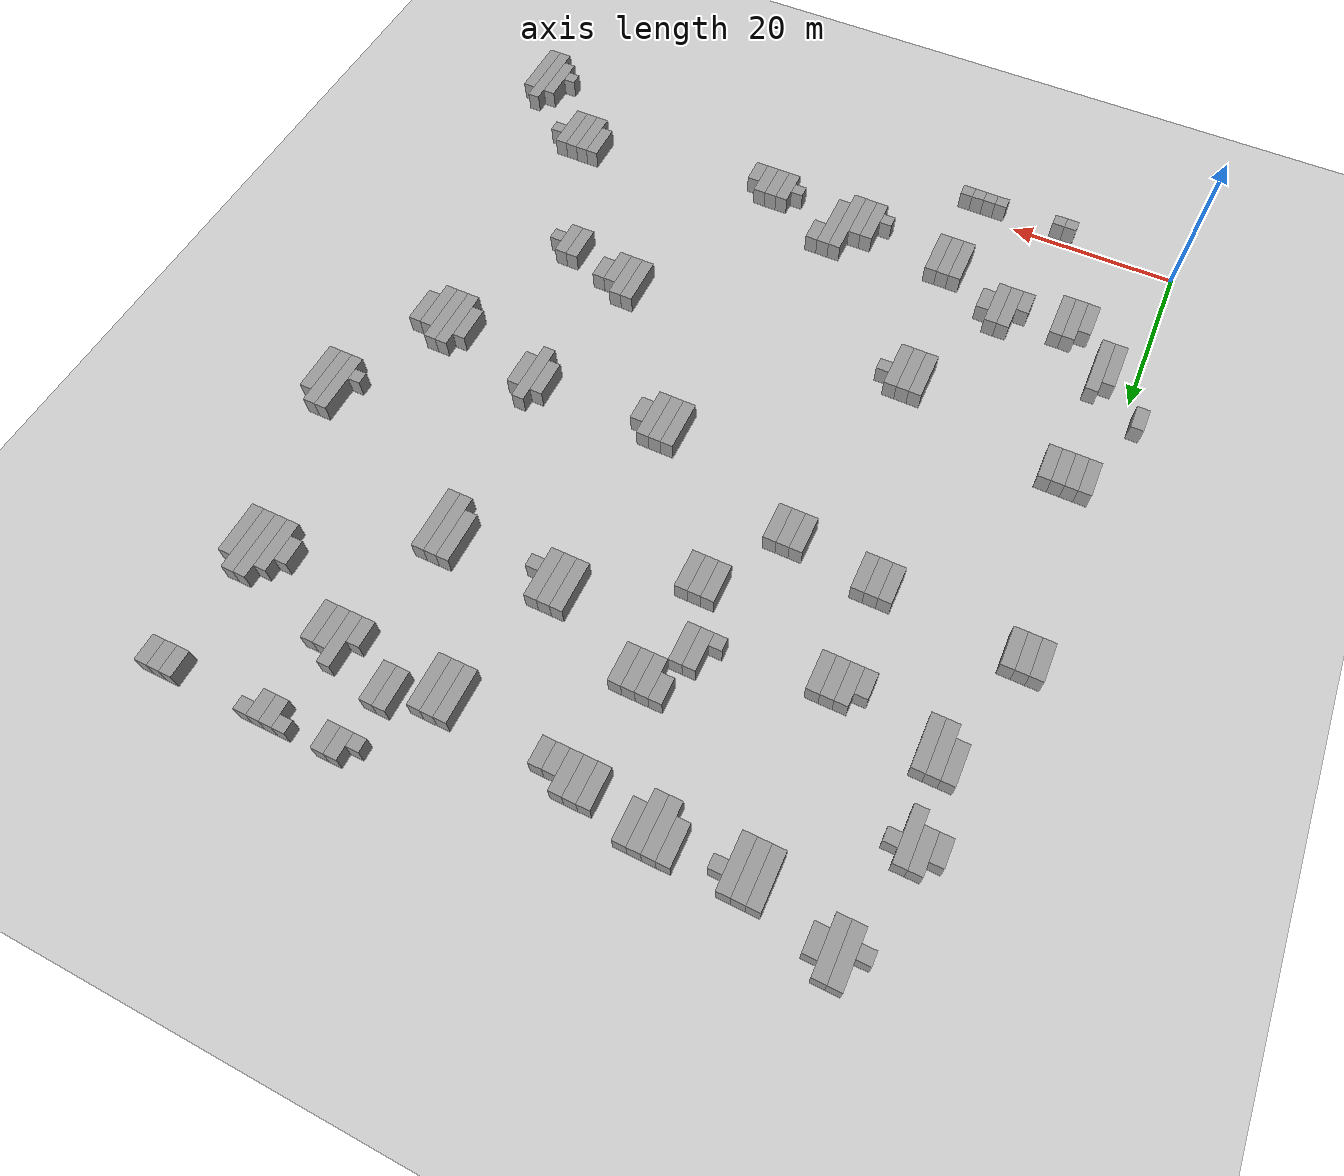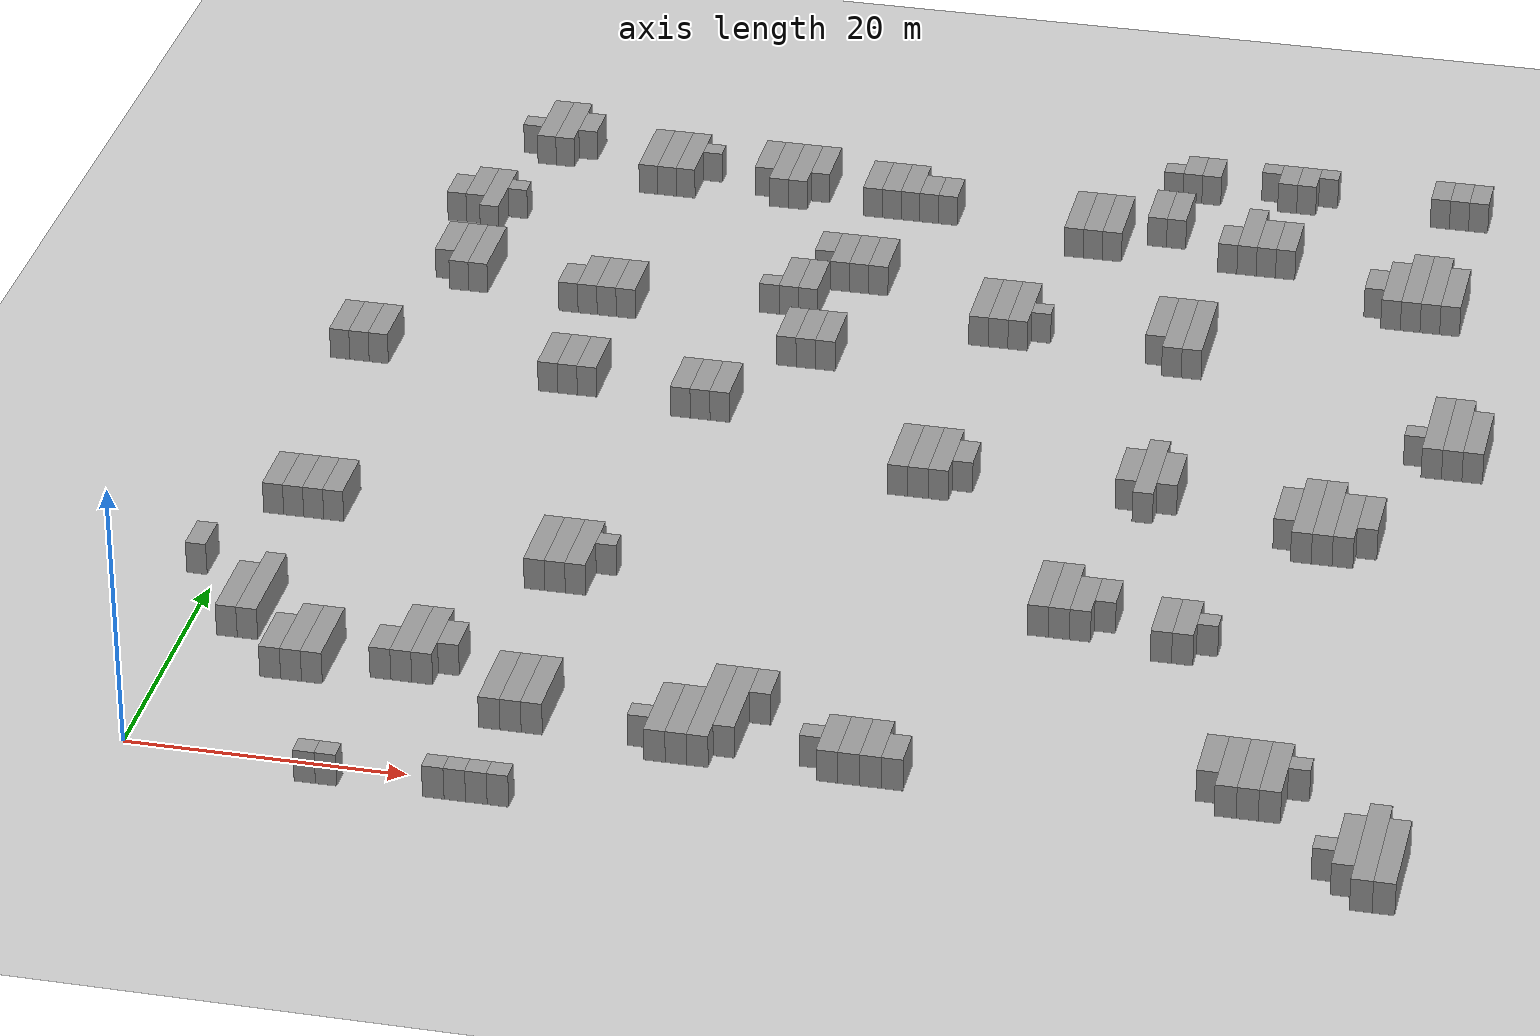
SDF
<?xml version='1.0'?>
        <sdf version='1.4'>
            <world name='1_wall'>
                <light name='sun' type='directional'>
                    <cast_shadows>1</cast_shadows>
                    <pose>0 0 10 0 -0 0</pose>
                    <diffuse>0.8 0.8 0.8 1</diffuse>
                    <specular>0.2 0.2 0.2 1</specular>
                    <attenuation>
                    <range>1000</range>
                    <constant>0.9</constant>
                    <linear>0.01</linear>
                    <quadratic>0.001</quadratic>
                    </attenuation>
                    <direction>-0.5 0.1 -0.9</direction>
                </light>
                <model name='ground_plane'>
                    <static>1</static>
                    <link name='link'>
                        <collision name='collision'>
                        <geometry>
                            <plane>
                                <normal>0 0 1</normal>
                                <size>1000 1000</size>
                            </plane>
                        </geometry>
                        <surface>
                            <friction>
                                <ode>
                                    <mu>100</mu>
                                    <mu2>50</mu2>
                                </ode>
                            </friction>
                            <bounce/>
                                <contact>
                                    <ode/>
                                </contact>
                        </surface>
                        <max_contacts>10</max_contacts>
                        </collision>
                    <visual name='visual'>
                        <cast_shadows>0</cast_shadows>
                        <geometry>
                            <plane>
                                <normal>0 0 1</normal>
                                <size>10000 10000</size>
                            </plane>
                            </geometry>
                                <material>
                                <script>
                                        <uri>file://media/materials/scripts/gazebo.material</uri>
                                        <name>Gazebo/Grey</name>
                                        </script>
                                    </material>
                    </visual>
                    <velocity_decay>
                        <linear>0</linear>
                        <angular>0</angular>
                    </velocity_decay>
                    <self_collide>0</self_collide>
                        <kinematic>0</kinematic>
                        <gravity>1</gravity>
                    </link>
                </model>
                <physics type='ode'>
                    <max_step_size>0.01</max_step_size>
                    <real_time_factor>1</real_time_factor>
                    <real_time_update_rate>100</real_time_update_rate>
                    <gravity>0 0 -9.8</gravity>
                </physics>
            <scene>
                <ambient>0.4 0.4 0.4 1</ambient>
                <background>0.7 0.7 0.7 1</background>
                <shadows>1</shadows>
            </scene>
    <model name='Wall_0'>
     <static>1</static>
    <link name='Wall_0'>
    <collision name='Wall_Collision_0'>
        <geometry>
          <box>
            <size>3.0 1.5 2.5</size>
          </box>
        </geometry>
        <pose>0 0 1.25 0 -0 0</pose>
      </collision>
      <visual name='Wall_Visual_0'>
        <pose>0 0 1.25 0 -0 0</pose>
        <geometry>
          <box>
            <size>3.0 1.5 2.5</size>
          </box>
        </geometry>
        <material>
          <script>
            <uri>file://media/materials/scripts/gazebo.material</uri>
            <name>Gazebo/Grey</name>
          </script>
        </material>
      </visual>
      <velocity_decay>
        <linear>0</linear>
        <angular>0</angular>
      </velocity_decay>
      <pose>-1.5 23.25 0 0 0 1.5707963267948966</pose>
    </link>
     </model><model name='Wall_1'>
     <static>1</static>
    <link name='Wall_1'>
    <collision name='Wall_Collision_1'>
        <geometry>
          <box>
            <size>4.5 1.5 2.5</size>
          </box>
        </geometry>
        <pose>0 0 1.25 0 -0 0</pose>
      </collision>
      <visual name='Wall_Visual_1'>
        <pose>0 0 1.25 0 -0 0</pose>
        <geometry>
          <box>
            <size>4.5 1.5 2.5</size>
          </box>
        </geometry>
        <material>
          <script>
            <uri>file://media/materials/scripts/gazebo.material</uri>
            <name>Gazebo/Grey</name>
          </script>
        </material>
      </visual>
      <velocity_decay>
        <linear>0</linear>
        <angular>0</angular>
      </velocity_decay>
      <pose>0.0 55.5 0 0 0 1.5707963267948966</pose>
    </link>
     </model><model name='Wall_2'>
     <static>1</static>
    <link name='Wall_2'>
    <collision name='Wall_Collision_2'>
        <geometry>
          <box>
            <size>4.5 1.5 2.5</size>
          </box>
        </geometry>
        <pose>0 0 1.25 0 -0 0</pose>
      </collision>
      <visual name='Wall_Visual_2'>
        <pose>0 0 1.25 0 -0 0</pose>
        <geometry>
          <box>
            <size>4.5 1.5 2.5</size>
          </box>
        </geometry>
        <material>
          <script>
            <uri>file://media/materials/scripts/gazebo.material</uri>
            <name>Gazebo/Grey</name>
          </script>
        </material>
      </visual>
      <velocity_decay>
        <linear>0</linear>
        <angular>0</angular>
      </velocity_decay>
      <pose>1.5 33.0 0 0 0 1.5707963267948966</pose>
    </link>
     </model><model name='Wall_3'>
     <static>1</static>
    <link name='Wall_3'>
    <collision name='Wall_Collision_3'>
        <geometry>
          <box>
            <size>4.5 1.5 2.5</size>
          </box>
        </geometry>
        <pose>0 0 1.25 0 -0 0</pose>
      </collision>
      <visual name='Wall_Visual_3'>
        <pose>0 0 1.25 0 -0 0</pose>
        <geometry>
          <box>
            <size>4.5 1.5 2.5</size>
          </box>
        </geometry>
        <material>
          <script>
            <uri>file://media/materials/scripts/gazebo.material</uri>
            <name>Gazebo/Grey</name>
          </script>
        </material>
      </visual>
      <velocity_decay>
        <linear>0</linear>
        <angular>0</angular>
      </velocity_decay>
      <pose>1.5 55.5 0 0 0 1.5707963267948966</pose>
    </link>
     </model><model name='Wall_4'>
     <static>1</static>
    <link name='Wall_4'>
    <collision name='Wall_Collision_4'>
        <geometry>
          <box>
            <size>6.0 1.5 2.5</size>
          </box>
        </geometry>
        <pose>0 0 1.25 0 -0 0</pose>
      </collision>
      <visual name='Wall_Visual_4'>
        <pose>0 0 1.25 0 -0 0</pose>
        <geometry>
          <box>
            <size>6.0 1.5 2.5</size>
          </box>
        </geometry>
        <material>
          <script>
            <uri>file://media/materials/scripts/gazebo.material</uri>
            <name>Gazebo/Grey</name>
          </script>
        </material>
      </visual>
      <velocity_decay>
        <linear>0</linear>
        <angular>0</angular>
      </velocity_decay>
      <pose>3.0 17.25 0 0 0 1.5707963267948966</pose>
    </link>
     </model><model name='Wall_5'>
     <static>1</static>
    <link name='Wall_5'>
    <collision name='Wall_Collision_5'>
        <geometry>
          <box>
            <size>4.5 1.5 2.5</size>
          </box>
        </geometry>
        <pose>0 0 1.25 0 -0 0</pose>
      </collision>
      <visual name='Wall_Visual_5'>
        <pose>0 0 1.25 0 -0 0</pose>
        <geometry>
          <box>
            <size>4.5 1.5 2.5</size>
          </box>
        </geometry>
        <material>
          <script>
            <uri>file://media/materials/scripts/gazebo.material</uri>
            <name>Gazebo/Grey</name>
          </script>
        </material>
      </visual>
      <velocity_decay>
        <linear>0</linear>
        <angular>0</angular>
      </velocity_decay>
      <pose>3.0 33.0 0 0 0 1.5707963267948966</pose>
    </link>
     </model><model name='Wall_6'>
     <static>1</static>
    <link name='Wall_6'>
    <collision name='Wall_Collision_6'>
        <geometry>
          <box>
            <size>4.5 1.5 2.5</size>
          </box>
        </geometry>
        <pose>0 0 1.25 0 -0 0</pose>
      </collision>
      <visual name='Wall_Visual_6'>
        <pose>0 0 1.25 0 -0 0</pose>
        <geometry>
          <box>
            <size>4.5 1.5 2.5</size>
          </box>
        </geometry>
        <material>
          <script>
            <uri>file://media/materials/scripts/gazebo.material</uri>
            <name>Gazebo/Grey</name>
          </script>
        </material>
      </visual>
      <velocity_decay>
        <linear>0</linear>
        <angular>0</angular>
      </velocity_decay>
      <pose>3.0 55.5 0 0 0 1.5707963267948966</pose>
    </link>
     </model><model name='Wall_7'>
     <static>1</static>
    <link name='Wall_7'>
    <collision name='Wall_Collision_7'>
        <geometry>
          <box>
            <size>3.0 1.5 2.5</size>
          </box>
        </geometry>
        <pose>0 0 1.25 0 -0 0</pose>
      </collision>
      <visual name='Wall_Visual_7'>
        <pose>0 0 1.25 0 -0 0</pose>
        <geometry>
          <box>
            <size>3.0 1.5 2.5</size>
          </box>
        </geometry>
        <material>
          <script>
            <uri>file://media/materials/scripts/gazebo.material</uri>
            <name>Gazebo/Grey</name>
          </script>
        </material>
      </visual>
      <velocity_decay>
        <linear>0</linear>
        <angular>0</angular>
      </velocity_decay>
      <pose>3.0 77.25 0 0 0 1.5707963267948966</pose>
    </link>
     </model><model name='Wall_8'>
     <static>1</static>
    <link name='Wall_8'>
    <collision name='Wall_Collision_8'>
        <geometry>
          <box>
            <size>7.5 1.5 2.5</size>
          </box>
        </geometry>
        <pose>0 0 1.25 0 -0 0</pose>
      </collision>
      <visual name='Wall_Visual_8'>
        <pose>0 0 1.25 0 -0 0</pose>
        <geometry>
          <box>
            <size>7.5 1.5 2.5</size>
          </box>
        </geometry>
        <material>
          <script>
            <uri>file://media/materials/scripts/gazebo.material</uri>
            <name>Gazebo/Grey</name>
          </script>
        </material>
      </visual>
      <velocity_decay>
        <linear>0</linear>
        <angular>0</angular>
      </velocity_decay>
      <pose>4.5 18.0 0 0 0 1.5707963267948966</pose>
    </link>
     </model><model name='Wall_9'>
     <static>1</static>
    <link name='Wall_9'>
    <collision name='Wall_Collision_9'>
        <geometry>
          <box>
            <size>4.5 1.5 2.5</size>
          </box>
        </geometry>
        <pose>0 0 1.25 0 -0 0</pose>
      </collision>
      <visual name='Wall_Visual_9'>
        <pose>0 0 1.25 0 -0 0</pose>
        <geometry>
          <box>
            <size>4.5 1.5 2.5</size>
          </box>
        </geometry>
        <material>
          <script>
            <uri>file://media/materials/scripts/gazebo.material</uri>
            <name>Gazebo/Grey</name>
          </script>
        </material>
      </visual>
      <velocity_decay>
        <linear>0</linear>
        <angular>0</angular>
      </velocity_decay>
      <pose>4.5 33.0 0 0 0 1.5707963267948966</pose>
    </link>
     </model><model name='Wall_10'>
     <static>1</static>
    <link name='Wall_10'>
    <collision name='Wall_Collision_10'>
        <geometry>
          <box>
            <size>4.5 1.5 2.5</size>
          </box>
        </geometry>
        <pose>0 0 1.25 0 -0 0</pose>
      </collision>
      <visual name='Wall_Visual_10'>
        <pose>0 0 1.25 0 -0 0</pose>
        <geometry>
          <box>
            <size>4.5 1.5 2.5</size>
          </box>
        </geometry>
        <material>
          <script>
            <uri>file://media/materials/scripts/gazebo.material</uri>
            <name>Gazebo/Grey</name>
          </script>
        </material>
      </visual>
      <velocity_decay>
        <linear>0</linear>
        <angular>0</angular>
      </velocity_decay>
      <pose>4.5 69.0 0 0 0 1.5707963267948966</pose>
    </link>
     </model><model name='Wall_11'>
     <static>1</static>
    <link name='Wall_11'>
    <collision name='Wall_Collision_11'>
        <geometry>
          <box>
            <size>4.5 1.5 2.5</size>
          </box>
        </geometry>
        <pose>0 0 1.25 0 -0 0</pose>
      </collision>
      <visual name='Wall_Visual_11'>
        <pose>0 0 1.25 0 -0 0</pose>
        <geometry>
          <box>
            <size>4.5 1.5 2.5</size>
          </box>
        </geometry>
        <material>
          <script>
            <uri>file://media/materials/scripts/gazebo.material</uri>
            <name>Gazebo/Grey</name>
          </script>
        </material>
      </visual>
      <velocity_decay>
        <linear>0</linear>
        <angular>0</angular>
      </velocity_decay>
      <pose>4.5 78.0 0 0 0 1.5707963267948966</pose>
    </link>
     </model><model name='Wall_12'>
     <static>1</static>
    <link name='Wall_12'>
    <collision name='Wall_Collision_12'>
        <geometry>
          <box>
            <size>4.5 1.5 2.5</size>
          </box>
        </geometry>
        <pose>0 0 1.25 0 -0 0</pose>
      </collision>
      <visual name='Wall_Visual_12'>
        <pose>0 0 1.25 0 -0 0</pose>
        <geometry>
          <box>
            <size>4.5 1.5 2.5</size>
          </box>
        </geometry>
        <material>
          <script>
            <uri>file://media/materials/scripts/gazebo.material</uri>
            <name>Gazebo/Grey</name>
          </script>
        </material>
      </visual>
      <velocity_decay>
        <linear>0</linear>
        <angular>0</angular>
      </velocity_decay>
      <pose>6.0 33.0 0 0 0 1.5707963267948966</pose>
    </link>
     </model><model name='Wall_13'>
     <static>1</static>
    <link name='Wall_13'>
    <collision name='Wall_Collision_13'>
        <geometry>
          <box>
            <size>6.0 1.5 2.5</size>
          </box>
        </geometry>
        <pose>0 0 1.25 0 -0 0</pose>
      </collision>
      <visual name='Wall_Visual_13'>
        <pose>0 0 1.25 0 -0 0</pose>
        <geometry>
          <box>
            <size>6.0 1.5 2.5</size>
          </box>
        </geometry>
        <material>
          <script>
            <uri>file://media/materials/scripts/gazebo.material</uri>
            <name>Gazebo/Grey</name>
          </script>
        </material>
      </visual>
      <velocity_decay>
        <linear>0</linear>
        <angular>0</angular>
      </velocity_decay>
      <pose>6.0 68.25 0 0 0 1.5707963267948966</pose>
    </link>
     </model><model name='Wall_14'>
     <static>1</static>
    <link name='Wall_14'>
    <collision name='Wall_Collision_14'>
        <geometry>
          <box>
            <size>6.0 1.5 2.5</size>
          </box>
        </geometry>
        <pose>0 0 1.25 0 -0 0</pose>
      </collision>
      <visual name='Wall_Visual_14'>
        <pose>0 0 1.25 0 -0 0</pose>
        <geometry>
          <box>
            <size>6.0 1.5 2.5</size>
          </box>
        </geometry>
        <material>
          <script>
            <uri>file://media/materials/scripts/gazebo.material</uri>
            <name>Gazebo/Grey</name>
          </script>
        </material>
      </visual>
      <velocity_decay>
        <linear>0</linear>
        <angular>0</angular>
      </velocity_decay>
      <pose>6.0 77.25 0 0 0 1.5707963267948966</pose>
    </link>
     </model><model name='Wall_15'>
     <static>1</static>
    <link name='Wall_15'>
    <collision name='Wall_Collision_15'>
        <geometry>
          <box>
            <size>1.5 1.5 2.5</size>
          </box>
        </geometry>
        <pose>0 0 1.25 0 -0 0</pose>
      </collision>
      <visual name='Wall_Visual_15'>
        <pose>0 0 1.25 0 -0 0</pose>
        <geometry>
          <box>
            <size>1.5 1.5 2.5</size>
          </box>
        </geometry>
        <material>
          <script>
            <uri>file://media/materials/scripts/gazebo.material</uri>
            <name>Gazebo/Grey</name>
          </script>
        </material>
      </visual>
      <velocity_decay>
        <linear>0</linear>
        <angular>0</angular>
      </velocity_decay>
      <pose>6.0 88.5 0 0 0 1.5707963267948966</pose>
    </link>
     </model><model name='Wall_16'>
     <static>1</static>
    <link name='Wall_16'>
    <collision name='Wall_Collision_16'>
        <geometry>
          <box>
            <size>4.5 1.5 2.5</size>
          </box>
        </geometry>
        <pose>0 0 1.25 0 -0 0</pose>
      </collision>
      <visual name='Wall_Visual_16'>
        <pose>0 0 1.25 0 -0 0</pose>
        <geometry>
          <box>
            <size>4.5 1.5 2.5</size>
          </box>
        </geometry>
        <material>
          <script>
            <uri>file://media/materials/scripts/gazebo.material</uri>
            <name>Gazebo/Grey</name>
          </script>
        </material>
      </visual>
      <velocity_decay>
        <linear>0</linear>
        <angular>0</angular>
      </velocity_decay>
      <pose>7.5 12.0 0 0 0 1.5707963267948966</pose>
    </link>
     </model><model name='Wall_17'>
     <static>1</static>
    <link name='Wall_17'>
    <collision name='Wall_Collision_17'>
        <geometry>
          <box>
            <size>6.0 1.5 2.5</size>
          </box>
        </geometry>
        <pose>0 0 1.25 0 -0 0</pose>
      </collision>
      <visual name='Wall_Visual_17'>
        <pose>0 0 1.25 0 -0 0</pose>
        <geometry>
          <box>
            <size>6.0 1.5 2.5</size>
          </box>
        </geometry>
        <material>
          <script>
            <uri>file://media/materials/scripts/gazebo.material</uri>
            <name>Gazebo/Grey</name>
          </script>
        </material>
      </visual>
      <velocity_decay>
        <linear>0</linear>
        <angular>0</angular>
      </velocity_decay>
      <pose>7.5 68.25 0 0 0 1.5707963267948966</pose>
    </link>
     </model><model name='Wall_18'>
     <static>1</static>
    <link name='Wall_18'>
    <collision name='Wall_Collision_18'>
        <geometry>
          <box>
            <size>1.5 1.5 2.5</size>
          </box>
        </geometry>
        <pose>0 0 1.25 0 -0 0</pose>
      </collision>
      <visual name='Wall_Visual_18'>
        <pose>0 0 1.25 0 -0 0</pose>
        <geometry>
          <box>
            <size>1.5 1.5 2.5</size>
          </box>
        </geometry>
        <material>
          <script>
            <uri>file://media/materials/scripts/gazebo.material</uri>
            <name>Gazebo/Grey</name>
          </script>
        </material>
      </visual>
      <velocity_decay>
        <linear>0</linear>
        <angular>0</angular>
      </velocity_decay>
      <pose>7.5 78.0 0 0 0 1.5707963267948966</pose>
    </link>
     </model><model name='Wall_19'>
     <static>1</static>
    <link name='Wall_19'>
    <collision name='Wall_Collision_19'>
        <geometry>
          <box>
            <size>6.0 1.5 2.5</size>
          </box>
        </geometry>
        <pose>0 0 1.25 0 -0 0</pose>
      </collision>
      <visual name='Wall_Visual_19'>
        <pose>0 0 1.25 0 -0 0</pose>
        <geometry>
          <box>
            <size>6.0 1.5 2.5</size>
          </box>
        </geometry>
        <material>
          <script>
            <uri>file://media/materials/scripts/gazebo.material</uri>
            <name>Gazebo/Grey</name>
          </script>
        </material>
      </visual>
      <velocity_decay>
        <linear>0</linear>
        <angular>0</angular>
      </velocity_decay>
      <pose>7.5 89.25 0 0 0 1.5707963267948966</pose>
    </link>
     </model><model name='Wall_20'>
     <static>1</static>
    <link name='Wall_20'>
    <collision name='Wall_Collision_20'>
        <geometry>
          <box>
            <size>6.0 1.5 2.5</size>
          </box>
        </geometry>
        <pose>0 0 1.25 0 -0 0</pose>
      </collision>
      <visual name='Wall_Visual_20'>
        <pose>0 0 1.25 0 -0 0</pose>
        <geometry>
          <box>
            <size>6.0 1.5 2.5</size>
          </box>
        </geometry>
        <material>
          <script>
            <uri>file://media/materials/scripts/gazebo.material</uri>
            <name>Gazebo/Grey</name>
          </script>
        </material>
      </visual>
      <velocity_decay>
        <linear>0</linear>
        <angular>0</angular>
      </velocity_decay>
      <pose>9.0 12.75 0 0 0 1.5707963267948966</pose>
    </link>
     </model><model name='Wall_21'>
     <static>1</static>
    <link name='Wall_21'>
    <collision name='Wall_Collision_21'>
        <geometry>
          <box>
            <size>6.0 1.5 2.5</size>
          </box>
        </geometry>
        <pose>0 0 1.25 0 -0 0</pose>
      </collision>
      <visual name='Wall_Visual_21'>
        <pose>0 0 1.25 0 -0 0</pose>
        <geometry>
          <box>
            <size>6.0 1.5 2.5</size>
          </box>
        </geometry>
        <material>
          <script>
            <uri>file://media/materials/scripts/gazebo.material</uri>
            <name>Gazebo/Grey</name>
          </script>
        </material>
      </visual>
      <velocity_decay>
        <linear>0</linear>
        <angular>0</angular>
      </velocity_decay>
      <pose>9.0 89.25 0 0 0 1.5707963267948966</pose>
    </link>
     </model><model name='Wall_22'>
     <static>1</static>
    <link name='Wall_22'>
    <collision name='Wall_Collision_22'>
        <geometry>
          <box>
            <size>6.0 1.5 2.5</size>
          </box>
        </geometry>
        <pose>0 0 1.25 0 -0 0</pose>
      </collision>
      <visual name='Wall_Visual_22'>
        <pose>0 0 1.25 0 -0 0</pose>
        <geometry>
          <box>
            <size>6.0 1.5 2.5</size>
          </box>
        </geometry>
        <material>
          <script>
            <uri>file://media/materials/scripts/gazebo.material</uri>
            <name>Gazebo/Grey</name>
          </script>
        </material>
      </visual>
      <velocity_decay>
        <linear>0</linear>
        <angular>0</angular>
      </velocity_decay>
      <pose>10.5 12.75 0 0 0 1.5707963267948966</pose>
    </link>
     </model><model name='Wall_23'>
     <static>1</static>
    <link name='Wall_23'>
    <collision name='Wall_Collision_23'>
        <geometry>
          <box>
            <size>3.0 1.5 2.5</size>
          </box>
        </geometry>
        <pose>0 0 1.25 0 -0 0</pose>
      </collision>
      <visual name='Wall_Visual_23'>
        <pose>0 0 1.25 0 -0 0</pose>
        <geometry>
          <box>
            <size>3.0 1.5 2.5</size>
          </box>
        </geometry>
        <material>
          <script>
            <uri>file://media/materials/scripts/gazebo.material</uri>
            <name>Gazebo/Grey</name>
          </script>
        </material>
      </visual>
      <velocity_decay>
        <linear>0</linear>
        <angular>0</angular>
      </velocity_decay>
      <pose>10.5 89.25 0 0 0 1.5707963267948966</pose>
    </link>
     </model><model name='Wall_24'>
     <static>1</static>
    <link name='Wall_24'>
    <collision name='Wall_Collision_24'>
        <geometry>
          <box>
            <size>1.5 1.5 2.5</size>
          </box>
        </geometry>
        <pose>0 0 1.25 0 -0 0</pose>
      </collision>
      <visual name='Wall_Visual_24'>
        <pose>0 0 1.25 0 -0 0</pose>
        <geometry>
          <box>
            <size>1.5 1.5 2.5</size>
          </box>
        </geometry>
        <material>
          <script>
            <uri>file://media/materials/scripts/gazebo.material</uri>
            <name>Gazebo/Grey</name>
          </script>
        </material>
      </visual>
      <velocity_decay>
        <linear>0</linear>
        <angular>0</angular>
      </velocity_decay>
      <pose>13.5 -1.5 0 0 0 1.5707963267948966</pose>
    </link>
     </model><model name='Wall_25'>
     <static>1</static>
    <link name='Wall_25'>
    <collision name='Wall_Collision_25'>
        <geometry>
          <box>
            <size>1.5 1.5 2.5</size>
          </box>
        </geometry>
        <pose>0 0 1.25 0 -0 0</pose>
      </collision>
      <visual name='Wall_Visual_25'>
        <pose>0 0 1.25 0 -0 0</pose>
        <geometry>
          <box>
            <size>1.5 1.5 2.5</size>
          </box>
        </geometry>
        <material>
          <script>
            <uri>file://media/materials/scripts/gazebo.material</uri>
            <name>Gazebo/Grey</name>
          </script>
        </material>
      </visual>
      <velocity_decay>
        <linear>0</linear>
        <angular>0</angular>
      </velocity_decay>
      <pose>15.0 -1.5 0 0 0 1.5707963267948966</pose>
    </link>
     </model><model name='Wall_26'>
     <static>1</static>
    <link name='Wall_26'>
    <collision name='Wall_Collision_26'>
        <geometry>
          <box>
            <size>3.0 1.5 2.5</size>
          </box>
        </geometry>
        <pose>0 0 1.25 0 -0 0</pose>
      </collision>
      <visual name='Wall_Visual_26'>
        <pose>0 0 1.25 0 -0 0</pose>
        <geometry>
          <box>
            <size>3.0 1.5 2.5</size>
          </box>
        </geometry>
        <material>
          <script>
            <uri>file://media/materials/scripts/gazebo.material</uri>
            <name>Gazebo/Grey</name>
          </script>
        </material>
      </visual>
      <velocity_decay>
        <linear>0</linear>
        <angular>0</angular>
      </velocity_decay>
      <pose>15.0 12.75 0 0 0 1.5707963267948966</pose>
    </link>
     </model><model name='Wall_27'>
     <static>1</static>
    <link name='Wall_27'>
    <collision name='Wall_Collision_27'>
        <geometry>
          <box>
            <size>3.0 1.5 2.5</size>
          </box>
        </geometry>
        <pose>0 0 1.25 0 -0 0</pose>
      </collision>
      <visual name='Wall_Visual_27'>
        <pose>0 0 1.25 0 -0 0</pose>
        <geometry>
          <box>
            <size>3.0 1.5 2.5</size>
          </box>
        </geometry>
        <material>
          <script>
            <uri>file://media/materials/scripts/gazebo.material</uri>
            <name>Gazebo/Grey</name>
          </script>
        </material>
      </visual>
      <velocity_decay>
        <linear>0</linear>
        <angular>0</angular>
      </velocity_decay>
      <pose>15.0 65.25 0 0 0 1.5707963267948966</pose>
    </link>
     </model><model name='Wall_28'>
     <static>1</static>
    <link name='Wall_28'>
    <collision name='Wall_Collision_28'>
        <geometry>
          <box>
            <size>6.0 1.5 2.5</size>
          </box>
        </geometry>
        <pose>0 0 1.25 0 -0 0</pose>
      </collision>
      <visual name='Wall_Visual_28'>
        <pose>0 0 1.25 0 -0 0</pose>
        <geometry>
          <box>
            <size>6.0 1.5 2.5</size>
          </box>
        </geometry>
        <material>
          <script>
            <uri>file://media/materials/scripts/gazebo.material</uri>
            <name>Gazebo/Grey</name>
          </script>
        </material>
      </visual>
      <velocity_decay>
        <linear>0</linear>
        <angular>0</angular>
      </velocity_decay>
      <pose>16.5 14.25 0 0 0 1.5707963267948966</pose>
    </link>
     </model><model name='Wall_29'>
     <static>1</static>
    <link name='Wall_29'>
    <collision name='Wall_Collision_29'>
        <geometry>
          <box>
            <size>4.5 1.5 2.5</size>
          </box>
        </geometry>
        <pose>0 0 1.25 0 -0 0</pose>
      </collision>
      <visual name='Wall_Visual_29'>
        <pose>0 0 1.25 0 -0 0</pose>
        <geometry>
          <box>
            <size>4.5 1.5 2.5</size>
          </box>
        </geometry>
        <material>
          <script>
            <uri>file://media/materials/scripts/gazebo.material</uri>
            <name>Gazebo/Grey</name>
          </script>
        </material>
      </visual>
      <velocity_decay>
        <linear>0</linear>
        <angular>0</angular>
      </velocity_decay>
      <pose>16.5 54.0 0 0 0 1.5707963267948966</pose>
    </link>
     </model><model name='Wall_30'>
     <static>1</static>
    <link name='Wall_30'>
    <collision name='Wall_Collision_30'>
        <geometry>
          <box>
            <size>4.5 1.5 2.5</size>
          </box>
        </geometry>
        <pose>0 0 1.25 0 -0 0</pose>
      </collision>
      <visual name='Wall_Visual_30'>
        <pose>0 0 1.25 0 -0 0</pose>
        <geometry>
          <box>
            <size>4.5 1.5 2.5</size>
          </box>
        </geometry>
        <material>
          <script>
            <uri>file://media/materials/scripts/gazebo.material</uri>
            <name>Gazebo/Grey</name>
          </script>
        </material>
      </visual>
      <velocity_decay>
        <linear>0</linear>
        <angular>0</angular>
      </velocity_decay>
      <pose>16.5 66.0 0 0 0 1.5707963267948966</pose>
    </link>
     </model><model name='Wall_31'>
     <static>1</static>
    <link name='Wall_31'>
    <collision name='Wall_Collision_31'>
        <geometry>
          <box>
            <size>6.0 1.5 2.5</size>
          </box>
        </geometry>
        <pose>0 0 1.25 0 -0 0</pose>
      </collision>
      <visual name='Wall_Visual_31'>
        <pose>0 0 1.25 0 -0 0</pose>
        <geometry>
          <box>
            <size>6.0 1.5 2.5</size>
          </box>
        </geometry>
        <material>
          <script>
            <uri>file://media/materials/scripts/gazebo.material</uri>
            <name>Gazebo/Grey</name>
          </script>
        </material>
      </visual>
      <velocity_decay>
        <linear>0</linear>
        <angular>0</angular>
      </velocity_decay>
      <pose>16.5 86.25 0 0 0 1.5707963267948966</pose>
    </link>
     </model><model name='Wall_32'>
     <static>1</static>
    <link name='Wall_32'>
    <collision name='Wall_Collision_32'>
        <geometry>
          <box>
            <size>6.0 1.5 2.5</size>
          </box>
        </geometry>
        <pose>0 0 1.25 0 -0 0</pose>
      </collision>
      <visual name='Wall_Visual_32'>
        <pose>0 0 1.25 0 -0 0</pose>
        <geometry>
          <box>
            <size>6.0 1.5 2.5</size>
          </box>
        </geometry>
        <material>
          <script>
            <uri>file://media/materials/scripts/gazebo.material</uri>
            <name>Gazebo/Grey</name>
          </script>
        </material>
      </visual>
      <velocity_decay>
        <linear>0</linear>
        <angular>0</angular>
      </velocity_decay>
      <pose>18.0 14.25 0 0 0 1.5707963267948966</pose>
    </link>
     </model><model name='Wall_33'>
     <static>1</static>
    <link name='Wall_33'>
    <collision name='Wall_Collision_33'>
        <geometry>
          <box>
            <size>4.5 1.5 2.5</size>
          </box>
        </geometry>
        <pose>0 0 1.25 0 -0 0</pose>
      </collision>
      <visual name='Wall_Visual_33'>
        <pose>0 0 1.25 0 -0 0</pose>
        <geometry>
          <box>
            <size>4.5 1.5 2.5</size>
          </box>
        </geometry>
        <material>
          <script>
            <uri>file://media/materials/scripts/gazebo.material</uri>
            <name>Gazebo/Grey</name>
          </script>
        </material>
      </visual>
      <velocity_decay>
        <linear>0</linear>
        <angular>0</angular>
      </velocity_decay>
      <pose>18.0 54.0 0 0 0 1.5707963267948966</pose>
    </link>
     </model><model name='Wall_34'>
     <static>1</static>
    <link name='Wall_34'>
    <collision name='Wall_Collision_34'>
        <geometry>
          <box>
            <size>4.5 1.5 2.5</size>
          </box>
        </geometry>
        <pose>0 0 1.25 0 -0 0</pose>
      </collision>
      <visual name='Wall_Visual_34'>
        <pose>0 0 1.25 0 -0 0</pose>
        <geometry>
          <box>
            <size>4.5 1.5 2.5</size>
          </box>
        </geometry>
        <material>
          <script>
            <uri>file://media/materials/scripts/gazebo.material</uri>
            <name>Gazebo/Grey</name>
          </script>
        </material>
      </visual>
      <velocity_decay>
        <linear>0</linear>
        <angular>0</angular>
      </velocity_decay>
      <pose>18.0 66.0 0 0 0 1.5707963267948966</pose>
    </link>
     </model><model name='Wall_35'>
     <static>1</static>
    <link name='Wall_35'>
    <collision name='Wall_Collision_35'>
        <geometry>
          <box>
            <size>6.0 1.5 2.5</size>
          </box>
        </geometry>
        <pose>0 0 1.25 0 -0 0</pose>
      </collision>
      <visual name='Wall_Visual_35'>
        <pose>0 0 1.25 0 -0 0</pose>
        <geometry>
          <box>
            <size>6.0 1.5 2.5</size>
          </box>
        </geometry>
        <material>
          <script>
            <uri>file://media/materials/scripts/gazebo.material</uri>
            <name>Gazebo/Grey</name>
          </script>
        </material>
      </visual>
      <velocity_decay>
        <linear>0</linear>
        <angular>0</angular>
      </velocity_decay>
      <pose>18.0 86.25 0 0 0 1.5707963267948966</pose>
    </link>
     </model><model name='Wall_36'>
     <static>1</static>
    <link name='Wall_36'>
    <collision name='Wall_Collision_36'>
        <geometry>
          <box>
            <size>3.0 1.5 2.5</size>
          </box>
        </geometry>
        <pose>0 0 1.25 0 -0 0</pose>
      </collision>
      <visual name='Wall_Visual_36'>
        <pose>0 0 1.25 0 -0 0</pose>
        <geometry>
          <box>
            <size>3.0 1.5 2.5</size>
          </box>
        </geometry>
        <material>
          <script>
            <uri>file://media/materials/scripts/gazebo.material</uri>
            <name>Gazebo/Grey</name>
          </script>
        </material>
      </visual>
      <velocity_decay>
        <linear>0</linear>
        <angular>0</angular>
      </velocity_decay>
      <pose>19.5 14.25 0 0 0 1.5707963267948966</pose>
    </link>
     </model><model name='Wall_37'>
     <static>1</static>
    <link name='Wall_37'>
    <collision name='Wall_Collision_37'>
        <geometry>
          <box>
            <size>4.5 1.5 2.5</size>
          </box>
        </geometry>
        <pose>0 0 1.25 0 -0 0</pose>
      </collision>
      <visual name='Wall_Visual_37'>
        <pose>0 0 1.25 0 -0 0</pose>
        <geometry>
          <box>
            <size>4.5 1.5 2.5</size>
          </box>
        </geometry>
        <material>
          <script>
            <uri>file://media/materials/scripts/gazebo.material</uri>
            <name>Gazebo/Grey</name>
          </script>
        </material>
      </visual>
      <velocity_decay>
        <linear>0</linear>
        <angular>0</angular>
      </velocity_decay>
      <pose>19.5 54.0 0 0 0 1.5707963267948966</pose>
    </link>
     </model><model name='Wall_38'>
     <static>1</static>
    <link name='Wall_38'>
    <collision name='Wall_Collision_38'>
        <geometry>
          <box>
            <size>4.5 1.5 2.5</size>
          </box>
        </geometry>
        <pose>0 0 1.25 0 -0 0</pose>
      </collision>
      <visual name='Wall_Visual_38'>
        <pose>0 0 1.25 0 -0 0</pose>
        <geometry>
          <box>
            <size>4.5 1.5 2.5</size>
          </box>
        </geometry>
        <material>
          <script>
            <uri>file://media/materials/scripts/gazebo.material</uri>
            <name>Gazebo/Grey</name>
          </script>
        </material>
      </visual>
      <velocity_decay>
        <linear>0</linear>
        <angular>0</angular>
      </velocity_decay>
      <pose>19.5 66.0 0 0 0 1.5707963267948966</pose>
    </link>
     </model><model name='Wall_39'>
     <static>1</static>
    <link name='Wall_39'>
    <collision name='Wall_Collision_39'>
        <geometry>
          <box>
            <size>6.0 1.5 2.5</size>
          </box>
        </geometry>
        <pose>0 0 1.25 0 -0 0</pose>
      </collision>
      <visual name='Wall_Visual_39'>
        <pose>0 0 1.25 0 -0 0</pose>
        <geometry>
          <box>
            <size>6.0 1.5 2.5</size>
          </box>
        </geometry>
        <material>
          <script>
            <uri>file://media/materials/scripts/gazebo.material</uri>
            <name>Gazebo/Grey</name>
          </script>
        </material>
      </visual>
      <velocity_decay>
        <linear>0</linear>
        <angular>0</angular>
      </velocity_decay>
      <pose>19.5 86.25 0 0 0 1.5707963267948966</pose>
    </link>
     </model><model name='Wall_40'>
     <static>1</static>
    <link name='Wall_40'>
    <collision name='Wall_Collision_40'>
        <geometry>
          <box>
            <size>1.5 1.5 2.5</size>
          </box>
        </geometry>
        <pose>0 0 1.25 0 -0 0</pose>
      </collision>
      <visual name='Wall_Visual_40'>
        <pose>0 0 1.25 0 -0 0</pose>
        <geometry>
          <box>
            <size>1.5 1.5 2.5</size>
          </box>
        </geometry>
        <material>
          <script>
            <uri>file://media/materials/scripts/gazebo.material</uri>
            <name>Gazebo/Grey</name>
          </script>
        </material>
      </visual>
      <velocity_decay>
        <linear>0</linear>
        <angular>0</angular>
      </velocity_decay>
      <pose>21.0 87.0 0 0 0 1.5707963267948966</pose>
    </link>
     </model><model name='Wall_41'>
     <static>1</static>
    <link name='Wall_41'>
    <collision name='Wall_Collision_41'>
        <geometry>
          <box>
            <size>1.5 1.5 2.5</size>
          </box>
        </geometry>
        <pose>0 0 1.25 0 -0 0</pose>
      </collision>
      <visual name='Wall_Visual_41'>
        <pose>0 0 1.25 0 -0 0</pose>
        <geometry>
          <box>
            <size>1.5 1.5 2.5</size>
          </box>
        </geometry>
        <material>
          <script>
            <uri>file://media/materials/scripts/gazebo.material</uri>
            <name>Gazebo/Grey</name>
          </script>
        </material>
      </visual>
      <velocity_decay>
        <linear>0</linear>
        <angular>0</angular>
      </velocity_decay>
      <pose>22.5 -1.5 0 0 0 1.5707963267948966</pose>
    </link>
     </model><model name='Wall_42'>
     <static>1</static>
    <link name='Wall_42'>
    <collision name='Wall_Collision_42'>
        <geometry>
          <box>
            <size>6.0 1.5 2.5</size>
          </box>
        </geometry>
        <pose>0 0 1.25 0 -0 0</pose>
      </collision>
      <visual name='Wall_Visual_42'>
        <pose>0 0 1.25 0 -0 0</pose>
        <geometry>
          <box>
            <size>6.0 1.5 2.5</size>
          </box>
        </geometry>
        <material>
          <script>
            <uri>file://media/materials/scripts/gazebo.material</uri>
            <name>Gazebo/Grey</name>
          </script>
        </material>
      </visual>
      <velocity_decay>
        <linear>0</linear>
        <angular>0</angular>
      </velocity_decay>
      <pose>22.5 27.75 0 0 0 1.5707963267948966</pose>
    </link>
     </model><model name='Wall_43'>
     <static>1</static>
    <link name='Wall_43'>
    <collision name='Wall_Collision_43'>
        <geometry>
          <box>
            <size>1.5 1.5 2.5</size>
          </box>
        </geometry>
        <pose>0 0 1.25 0 -0 0</pose>
      </collision>
      <visual name='Wall_Visual_43'>
        <pose>0 0 1.25 0 -0 0</pose>
        <geometry>
          <box>
            <size>1.5 1.5 2.5</size>
          </box>
        </geometry>
        <material>
          <script>
            <uri>file://media/materials/scripts/gazebo.material</uri>
            <name>Gazebo/Grey</name>
          </script>
        </material>
      </visual>
      <velocity_decay>
        <linear>0</linear>
        <angular>0</angular>
      </velocity_decay>
      <pose>24.0 -1.5 0 0 0 1.5707963267948966</pose>
    </link>
     </model><model name='Wall_44'>
     <static>1</static>
    <link name='Wall_44'>
    <collision name='Wall_Collision_44'>
        <geometry>
          <box>
            <size>6.0 1.5 2.5</size>
          </box>
        </geometry>
        <pose>0 0 1.25 0 -0 0</pose>
      </collision>
      <visual name='Wall_Visual_44'>
        <pose>0 0 1.25 0 -0 0</pose>
        <geometry>
          <box>
            <size>6.0 1.5 2.5</size>
          </box>
        </geometry>
        <material>
          <script>
            <uri>file://media/materials/scripts/gazebo.material</uri>
            <name>Gazebo/Grey</name>
          </script>
        </material>
      </visual>
      <velocity_decay>
        <linear>0</linear>
        <angular>0</angular>
      </velocity_decay>
      <pose>24.0 9.75 0 0 0 1.5707963267948966</pose>
    </link>
     </model><model name='Wall_45'>
     <static>1</static>
    <link name='Wall_45'>
    <collision name='Wall_Collision_45'>
        <geometry>
          <box>
            <size>6.0 1.5 2.5</size>
          </box>
        </geometry>
        <pose>0 0 1.25 0 -0 0</pose>
      </collision>
      <visual name='Wall_Visual_45'>
        <pose>0 0 1.25 0 -0 0</pose>
        <geometry>
          <box>
            <size>6.0 1.5 2.5</size>
          </box>
        </geometry>
        <material>
          <script>
            <uri>file://media/materials/scripts/gazebo.material</uri>
            <name>Gazebo/Grey</name>
          </script>
        </material>
      </visual>
      <velocity_decay>
        <linear>0</linear>
        <angular>0</angular>
      </velocity_decay>
      <pose>24.0 27.75 0 0 0 1.5707963267948966</pose>
    </link>
     </model><model name='Wall_46'>
     <static>1</static>
    <link name='Wall_46'>
    <collision name='Wall_Collision_46'>
        <geometry>
          <box>
            <size>1.5 1.5 2.5</size>
          </box>
        </geometry>
        <pose>0 0 1.25 0 -0 0</pose>
      </collision>
      <visual name='Wall_Visual_46'>
        <pose>0 0 1.25 0 -0 0</pose>
        <geometry>
          <box>
            <size>1.5 1.5 2.5</size>
          </box>
        </geometry>
        <material>
          <script>
            <uri>file://media/materials/scripts/gazebo.material</uri>
            <name>Gazebo/Grey</name>
          </script>
        </material>
      </visual>
      <velocity_decay>
        <linear>0</linear>
        <angular>0</angular>
      </velocity_decay>
      <pose>25.5 -1.5 0 0 0 1.5707963267948966</pose>
    </link>
     </model><model name='Wall_47'>
     <static>1</static>
    <link name='Wall_47'>
    <collision name='Wall_Collision_47'>
        <geometry>
          <box>
            <size>6.0 1.5 2.5</size>
          </box>
        </geometry>
        <pose>0 0 1.25 0 -0 0</pose>
      </collision>
      <visual name='Wall_Visual_47'>
        <pose>0 0 1.25 0 -0 0</pose>
        <geometry>
          <box>
            <size>6.0 1.5 2.5</size>
          </box>
        </geometry>
        <material>
          <script>
            <uri>file://media/materials/scripts/gazebo.material</uri>
            <name>Gazebo/Grey</name>
          </script>
        </material>
      </visual>
      <velocity_decay>
        <linear>0</linear>
        <angular>0</angular>
      </velocity_decay>
      <pose>25.5 9.75 0 0 0 1.5707963267948966</pose>
    </link>
     </model><model name='Wall_48'>
     <static>1</static>
    <link name='Wall_48'>
    <collision name='Wall_Collision_48'>
        <geometry>
          <box>
            <size>6.0 1.5 2.5</size>
          </box>
        </geometry>
        <pose>0 0 1.25 0 -0 0</pose>
      </collision>
      <visual name='Wall_Visual_48'>
        <pose>0 0 1.25 0 -0 0</pose>
        <geometry>
          <box>
            <size>6.0 1.5 2.5</size>
          </box>
        </geometry>
        <material>
          <script>
            <uri>file://media/materials/scripts/gazebo.material</uri>
            <name>Gazebo/Grey</name>
          </script>
        </material>
      </visual>
      <velocity_decay>
        <linear>0</linear>
        <angular>0</angular>
      </velocity_decay>
      <pose>25.5 27.75 0 0 0 1.5707963267948966</pose>
    </link>
     </model><model name='Wall_49'>
     <static>1</static>
    <link name='Wall_49'>
    <collision name='Wall_Collision_49'>
        <geometry>
          <box>
            <size>4.5 1.5 2.5</size>
          </box>
        </geometry>
        <pose>0 0 1.25 0 -0 0</pose>
      </collision>
      <visual name='Wall_Visual_49'>
        <pose>0 0 1.25 0 -0 0</pose>
        <geometry>
          <box>
            <size>4.5 1.5 2.5</size>
          </box>
        </geometry>
        <material>
          <script>
            <uri>file://media/materials/scripts/gazebo.material</uri>
            <name>Gazebo/Grey</name>
          </script>
        </material>
      </visual>
      <velocity_decay>
        <linear>0</linear>
        <angular>0</angular>
      </velocity_decay>
      <pose>25.5 87.0 0 0 0 1.5707963267948966</pose>
    </link>
     </model><model name='Wall_50'>
     <static>1</static>
    <link name='Wall_50'>
    <collision name='Wall_Collision_50'>
        <geometry>
          <box>
            <size>1.5 1.5 2.5</size>
          </box>
        </geometry>
        <pose>0 0 1.25 0 -0 0</pose>
      </collision>
      <visual name='Wall_Visual_50'>
        <pose>0 0 1.25 0 -0 0</pose>
        <geometry>
          <box>
            <size>1.5 1.5 2.5</size>
          </box>
        </geometry>
        <material>
          <script>
            <uri>file://media/materials/scripts/gazebo.material</uri>
            <name>Gazebo/Grey</name>
          </script>
        </material>
      </visual>
      <velocity_decay>
        <linear>0</linear>
        <angular>0</angular>
      </velocity_decay>
      <pose>27.0 -1.5 0 0 0 1.5707963267948966</pose>
    </link>
     </model><model name='Wall_51'>
     <static>1</static>
    <link name='Wall_51'>
    <collision name='Wall_Collision_51'>
        <geometry>
          <box>
            <size>6.0 1.5 2.5</size>
          </box>
        </geometry>
        <pose>0 0 1.25 0 -0 0</pose>
      </collision>
      <visual name='Wall_Visual_51'>
        <pose>0 0 1.25 0 -0 0</pose>
        <geometry>
          <box>
            <size>6.0 1.5 2.5</size>
          </box>
        </geometry>
        <material>
          <script>
            <uri>file://media/materials/scripts/gazebo.material</uri>
            <name>Gazebo/Grey</name>
          </script>
        </material>
      </visual>
      <velocity_decay>
        <linear>0</linear>
        <angular>0</angular>
      </velocity_decay>
      <pose>27.0 9.75 0 0 0 1.5707963267948966</pose>
    </link>
     </model><model name='Wall_52'>
     <static>1</static>
    <link name='Wall_52'>
    <collision name='Wall_Collision_52'>
        <geometry>
          <box>
            <size>1.5 1.5 2.5</size>
          </box>
        </geometry>
        <pose>0 0 1.25 0 -0 0</pose>
      </collision>
      <visual name='Wall_Visual_52'>
        <pose>0 0 1.25 0 -0 0</pose>
        <geometry>
          <box>
            <size>1.5 1.5 2.5</size>
          </box>
        </geometry>
        <material>
          <script>
            <uri>file://media/materials/scripts/gazebo.material</uri>
            <name>Gazebo/Grey</name>
          </script>
        </material>
      </visual>
      <velocity_decay>
        <linear>0</linear>
        <angular>0</angular>
      </velocity_decay>
      <pose>27.0 28.5 0 0 0 1.5707963267948966</pose>
    </link>
     </model><model name='Wall_53'>
     <static>1</static>
    <link name='Wall_53'>
    <collision name='Wall_Collision_53'>
        <geometry>
          <box>
            <size>4.5 1.5 2.5</size>
          </box>
        </geometry>
        <pose>0 0 1.25 0 -0 0</pose>
      </collision>
      <visual name='Wall_Visual_53'>
        <pose>0 0 1.25 0 -0 0</pose>
        <geometry>
          <box>
            <size>4.5 1.5 2.5</size>
          </box>
        </geometry>
        <material>
          <script>
            <uri>file://media/materials/scripts/gazebo.material</uri>
            <name>Gazebo/Grey</name>
          </script>
        </material>
      </visual>
      <velocity_decay>
        <linear>0</linear>
        <angular>0</angular>
      </velocity_decay>
      <pose>27.0 52.5 0 0 0 1.5707963267948966</pose>
    </link>
     </model><model name='Wall_54'>
     <static>1</static>
    <link name='Wall_54'>
    <collision name='Wall_Collision_54'>
        <geometry>
          <box>
            <size>6.0 1.5 2.5</size>
          </box>
        </geometry>
        <pose>0 0 1.25 0 -0 0</pose>
      </collision>
      <visual name='Wall_Visual_54'>
        <pose>0 0 1.25 0 -0 0</pose>
        <geometry>
          <box>
            <size>6.0 1.5 2.5</size>
          </box>
        </geometry>
        <material>
          <script>
            <uri>file://media/materials/scripts/gazebo.material</uri>
            <name>Gazebo/Grey</name>
          </script>
        </material>
      </visual>
      <velocity_decay>
        <linear>0</linear>
        <angular>0</angular>
      </velocity_decay>
      <pose>27.0 86.25 0 0 0 1.5707963267948966</pose>
    </link>
     </model><model name='Wall_55'>
     <static>1</static>
    <link name='Wall_55'>
    <collision name='Wall_Collision_55'>
        <geometry>
          <box>
            <size>4.5 1.5 2.5</size>
          </box>
        </geometry>
        <pose>0 0 1.25 0 -0 0</pose>
      </collision>
      <visual name='Wall_Visual_55'>
        <pose>0 0 1.25 0 -0 0</pose>
        <geometry>
          <box>
            <size>4.5 1.5 2.5</size>
          </box>
        </geometry>
        <material>
          <script>
            <uri>file://media/materials/scripts/gazebo.material</uri>
            <name>Gazebo/Grey</name>
          </script>
        </material>
      </visual>
      <velocity_decay>
        <linear>0</linear>
        <angular>0</angular>
      </velocity_decay>
      <pose>28.5 52.5 0 0 0 1.5707963267948966</pose>
    </link>
     </model><model name='Wall_56'>
     <static>1</static>
    <link name='Wall_56'>
    <collision name='Wall_Collision_56'>
        <geometry>
          <box>
            <size>6.0 1.5 2.5</size>
          </box>
        </geometry>
        <pose>0 0 1.25 0 -0 0</pose>
      </collision>
      <visual name='Wall_Visual_56'>
        <pose>0 0 1.25 0 -0 0</pose>
        <geometry>
          <box>
            <size>6.0 1.5 2.5</size>
          </box>
        </geometry>
        <material>
          <script>
            <uri>file://media/materials/scripts/gazebo.material</uri>
            <name>Gazebo/Grey</name>
          </script>
        </material>
      </visual>
      <velocity_decay>
        <linear>0</linear>
        <angular>0</angular>
      </velocity_decay>
      <pose>28.5 86.25 0 0 0 1.5707963267948966</pose>
    </link>
     </model><model name='Wall_57'>
     <static>1</static>
    <link name='Wall_57'>
    <collision name='Wall_Collision_57'>
        <geometry>
          <box>
            <size>4.5 1.5 2.5</size>
          </box>
        </geometry>
        <pose>0 0 1.25 0 -0 0</pose>
      </collision>
      <visual name='Wall_Visual_57'>
        <pose>0 0 1.25 0 -0 0</pose>
        <geometry>
          <box>
            <size>4.5 1.5 2.5</size>
          </box>
        </geometry>
        <material>
          <script>
            <uri>file://media/materials/scripts/gazebo.material</uri>
            <name>Gazebo/Grey</name>
          </script>
        </material>
      </visual>
      <velocity_decay>
        <linear>0</linear>
        <angular>0</angular>
      </velocity_decay>
      <pose>30.0 52.5 0 0 0 1.5707963267948966</pose>
    </link>
     </model><model name='Wall_58'>
     <static>1</static>
    <link name='Wall_58'>
    <collision name='Wall_Collision_58'>
        <geometry>
          <box>
            <size>1.5 1.5 2.5</size>
          </box>
        </geometry>
        <pose>0 0 1.25 0 -0 0</pose>
      </collision>
      <visual name='Wall_Visual_58'>
        <pose>0 0 1.25 0 -0 0</pose>
        <geometry>
          <box>
            <size>1.5 1.5 2.5</size>
          </box>
        </geometry>
        <material>
          <script>
            <uri>file://media/materials/scripts/gazebo.material</uri>
            <name>Gazebo/Grey</name>
          </script>
        </material>
      </visual>
      <velocity_decay>
        <linear>0</linear>
        <angular>0</angular>
      </velocity_decay>
      <pose>30.0 67.5 0 0 0 1.5707963267948966</pose>
    </link>
     </model><model name='Wall_59'>
     <static>1</static>
    <link name='Wall_59'>
    <collision name='Wall_Collision_59'>
        <geometry>
          <box>
            <size>4.5 1.5 2.5</size>
          </box>
        </geometry>
        <pose>0 0 1.25 0 -0 0</pose>
      </collision>
      <visual name='Wall_Visual_59'>
        <pose>0 0 1.25 0 -0 0</pose>
        <geometry>
          <box>
            <size>4.5 1.5 2.5</size>
          </box>
        </geometry>
        <material>
          <script>
            <uri>file://media/materials/scripts/gazebo.material</uri>
            <name>Gazebo/Grey</name>
          </script>
        </material>
      </visual>
      <velocity_decay>
        <linear>0</linear>
        <angular>0</angular>
      </velocity_decay>
      <pose>30.0 87.0 0 0 0 1.5707963267948966</pose>
    </link>
     </model><model name='Wall_60'>
     <static>1</static>
    <link name='Wall_60'>
    <collision name='Wall_Collision_60'>
        <geometry>
          <box>
            <size>4.5 1.5 2.5</size>
          </box>
        </geometry>
        <pose>0 0 1.25 0 -0 0</pose>
      </collision>
      <visual name='Wall_Visual_60'>
        <pose>0 0 1.25 0 -0 0</pose>
        <geometry>
          <box>
            <size>4.5 1.5 2.5</size>
          </box>
        </geometry>
        <material>
          <script>
            <uri>file://media/materials/scripts/gazebo.material</uri>
            <name>Gazebo/Grey</name>
          </script>
        </material>
      </visual>
      <velocity_decay>
        <linear>0</linear>
        <angular>0</angular>
      </velocity_decay>
      <pose>31.5 69.0 0 0 0 1.5707963267948966</pose>
    </link>
     </model><model name='Wall_61'>
     <static>1</static>
    <link name='Wall_61'>
    <collision name='Wall_Collision_61'>
        <geometry>
          <box>
            <size>4.5 1.5 2.5</size>
          </box>
        </geometry>
        <pose>0 0 1.25 0 -0 0</pose>
      </collision>
      <visual name='Wall_Visual_61'>
        <pose>0 0 1.25 0 -0 0</pose>
        <geometry>
          <box>
            <size>4.5 1.5 2.5</size>
          </box>
        </geometry>
        <material>
          <script>
            <uri>file://media/materials/scripts/gazebo.material</uri>
            <name>Gazebo/Grey</name>
          </script>
        </material>
      </visual>
      <velocity_decay>
        <linear>0</linear>
        <angular>0</angular>
      </velocity_decay>
      <pose>33.0 61.5 0 0 0 1.5707963267948966</pose>
    </link>
     </model><model name='Wall_62'>
     <static>1</static>
    <link name='Wall_62'>
    <collision name='Wall_Collision_62'>
        <geometry>
          <box>
            <size>4.5 1.5 2.5</size>
          </box>
        </geometry>
        <pose>0 0 1.25 0 -0 0</pose>
      </collision>
      <visual name='Wall_Visual_62'>
        <pose>0 0 1.25 0 -0 0</pose>
        <geometry>
          <box>
            <size>4.5 1.5 2.5</size>
          </box>
        </geometry>
        <material>
          <script>
            <uri>file://media/materials/scripts/gazebo.material</uri>
            <name>Gazebo/Grey</name>
          </script>
        </material>
      </visual>
      <velocity_decay>
        <linear>0</linear>
        <angular>0</angular>
      </velocity_decay>
      <pose>33.0 69.0 0 0 0 1.5707963267948966</pose>
    </link>
     </model><model name='Wall_63'>
     <static>1</static>
    <link name='Wall_63'>
    <collision name='Wall_Collision_63'>
        <geometry>
          <box>
            <size>3.0 1.5 2.5</size>
          </box>
        </geometry>
        <pose>0 0 1.25 0 -0 0</pose>
      </collision>
      <visual name='Wall_Visual_63'>
        <pose>0 0 1.25 0 -0 0</pose>
        <geometry>
          <box>
            <size>3.0 1.5 2.5</size>
          </box>
        </geometry>
        <material>
          <script>
            <uri>file://media/materials/scripts/gazebo.material</uri>
            <name>Gazebo/Grey</name>
          </script>
        </material>
      </visual>
      <velocity_decay>
        <linear>0</linear>
        <angular>0</angular>
      </velocity_decay>
      <pose>33.0 74.25 0 0 0 1.5707963267948966</pose>
    </link>
     </model><model name='Wall_64'>
     <static>1</static>
    <link name='Wall_64'>
    <collision name='Wall_Collision_64'>
        <geometry>
          <box>
            <size>1.5 1.5 2.5</size>
          </box>
        </geometry>
        <pose>0 0 1.25 0 -0 0</pose>
      </collision>
      <visual name='Wall_Visual_64'>
        <pose>0 0 1.25 0 -0 0</pose>
        <geometry>
          <box>
            <size>1.5 1.5 2.5</size>
          </box>
        </geometry>
        <material>
          <script>
            <uri>file://media/materials/scripts/gazebo.material</uri>
            <name>Gazebo/Grey</name>
          </script>
        </material>
      </visual>
      <velocity_decay>
        <linear>0</linear>
        <angular>0</angular>
      </velocity_decay>
      <pose>34.5 7.5 0 0 0 1.5707963267948966</pose>
    </link>
     </model><model name='Wall_65'>
     <static>1</static>
    <link name='Wall_65'>
    <collision name='Wall_Collision_65'>
        <geometry>
          <box>
            <size>4.5 1.5 2.5</size>
          </box>
        </geometry>
        <pose>0 0 1.25 0 -0 0</pose>
      </collision>
      <visual name='Wall_Visual_65'>
        <pose>0 0 1.25 0 -0 0</pose>
        <geometry>
          <box>
            <size>4.5 1.5 2.5</size>
          </box>
        </geometry>
        <material>
          <script>
            <uri>file://media/materials/scripts/gazebo.material</uri>
            <name>Gazebo/Grey</name>
          </script>
        </material>
      </visual>
      <velocity_decay>
        <linear>0</linear>
        <angular>0</angular>
      </velocity_decay>
      <pose>34.5 61.5 0 0 0 1.5707963267948966</pose>
    </link>
     </model><model name='Wall_66'>
     <static>1</static>
    <link name='Wall_66'>
    <collision name='Wall_Collision_66'>
        <geometry>
          <box>
            <size>4.5 1.5 2.5</size>
          </box>
        </geometry>
        <pose>0 0 1.25 0 -0 0</pose>
      </collision>
      <visual name='Wall_Visual_66'>
        <pose>0 0 1.25 0 -0 0</pose>
        <geometry>
          <box>
            <size>4.5 1.5 2.5</size>
          </box>
        </geometry>
        <material>
          <script>
            <uri>file://media/materials/scripts/gazebo.material</uri>
            <name>Gazebo/Grey</name>
          </script>
        </material>
      </visual>
      <velocity_decay>
        <linear>0</linear>
        <angular>0</angular>
      </velocity_decay>
      <pose>34.5 73.5 0 0 0 1.5707963267948966</pose>
    </link>
     </model><model name='Wall_67'>
     <static>1</static>
    <link name='Wall_67'>
    <collision name='Wall_Collision_67'>
        <geometry>
          <box>
            <size>4.5 1.5 2.5</size>
          </box>
        </geometry>
        <pose>0 0 1.25 0 -0 0</pose>
      </collision>
      <visual name='Wall_Visual_67'>
        <pose>0 0 1.25 0 -0 0</pose>
        <geometry>
          <box>
            <size>4.5 1.5 2.5</size>
          </box>
        </geometry>
        <material>
          <script>
            <uri>file://media/materials/scripts/gazebo.material</uri>
            <name>Gazebo/Grey</name>
          </script>
        </material>
      </visual>
      <velocity_decay>
        <linear>0</linear>
        <angular>0</angular>
      </velocity_decay>
      <pose>34.5 85.5 0 0 0 1.5707963267948966</pose>
    </link>
     </model><model name='Wall_68'>
     <static>1</static>
    <link name='Wall_68'>
    <collision name='Wall_Collision_68'>
        <geometry>
          <box>
            <size>6.0 1.5 2.5</size>
          </box>
        </geometry>
        <pose>0 0 1.25 0 -0 0</pose>
      </collision>
      <visual name='Wall_Visual_68'>
        <pose>0 0 1.25 0 -0 0</pose>
        <geometry>
          <box>
            <size>6.0 1.5 2.5</size>
          </box>
        </geometry>
        <material>
          <script>
            <uri>file://media/materials/scripts/gazebo.material</uri>
            <name>Gazebo/Grey</name>
          </script>
        </material>
      </visual>
      <velocity_decay>
        <linear>0</linear>
        <angular>0</angular>
      </velocity_decay>
      <pose>36.0 8.25 0 0 0 1.5707963267948966</pose>
    </link>
     </model><model name='Wall_69'>
     <static>1</static>
    <link name='Wall_69'>
    <collision name='Wall_Collision_69'>
        <geometry>
          <box>
            <size>4.5 1.5 2.5</size>
          </box>
        </geometry>
        <pose>0 0 1.25 0 -0 0</pose>
      </collision>
      <visual name='Wall_Visual_69'>
        <pose>0 0 1.25 0 -0 0</pose>
        <geometry>
          <box>
            <size>4.5 1.5 2.5</size>
          </box>
        </geometry>
        <material>
          <script>
            <uri>file://media/materials/scripts/gazebo.material</uri>
            <name>Gazebo/Grey</name>
          </script>
        </material>
      </visual>
      <velocity_decay>
        <linear>0</linear>
        <angular>0</angular>
      </velocity_decay>
      <pose>36.0 61.5 0 0 0 1.5707963267948966</pose>
    </link>
     </model><model name='Wall_70'>
     <static>1</static>
    <link name='Wall_70'>
    <collision name='Wall_Collision_70'>
        <geometry>
          <box>
            <size>4.5 1.5 2.5</size>
          </box>
        </geometry>
        <pose>0 0 1.25 0 -0 0</pose>
      </collision>
      <visual name='Wall_Visual_70'>
        <pose>0 0 1.25 0 -0 0</pose>
        <geometry>
          <box>
            <size>4.5 1.5 2.5</size>
          </box>
        </geometry>
        <material>
          <script>
            <uri>file://media/materials/scripts/gazebo.material</uri>
            <name>Gazebo/Grey</name>
          </script>
        </material>
      </visual>
      <velocity_decay>
        <linear>0</linear>
        <angular>0</angular>
      </velocity_decay>
      <pose>36.0 73.5 0 0 0 1.5707963267948966</pose>
    </link>
     </model><model name='Wall_71'>
     <static>1</static>
    <link name='Wall_71'>
    <collision name='Wall_Collision_71'>
        <geometry>
          <box>
            <size>4.5 1.5 2.5</size>
          </box>
        </geometry>
        <pose>0 0 1.25 0 -0 0</pose>
      </collision>
      <visual name='Wall_Visual_71'>
        <pose>0 0 1.25 0 -0 0</pose>
        <geometry>
          <box>
            <size>4.5 1.5 2.5</size>
          </box>
        </geometry>
        <material>
          <script>
            <uri>file://media/materials/scripts/gazebo.material</uri>
            <name>Gazebo/Grey</name>
          </script>
        </material>
      </visual>
      <velocity_decay>
        <linear>0</linear>
        <angular>0</angular>
      </velocity_decay>
      <pose>36.0 85.5 0 0 0 1.5707963267948966</pose>
    </link>
     </model><model name='Wall_72'>
     <static>1</static>
    <link name='Wall_72'>
    <collision name='Wall_Collision_72'>
        <geometry>
          <box>
            <size>6.0 1.5 2.5</size>
          </box>
        </geometry>
        <pose>0 0 1.25 0 -0 0</pose>
      </collision>
      <visual name='Wall_Visual_72'>
        <pose>0 0 1.25 0 -0 0</pose>
        <geometry>
          <box>
            <size>6.0 1.5 2.5</size>
          </box>
        </geometry>
        <material>
          <script>
            <uri>file://media/materials/scripts/gazebo.material</uri>
            <name>Gazebo/Grey</name>
          </script>
        </material>
      </visual>
      <velocity_decay>
        <linear>0</linear>
        <angular>0</angular>
      </velocity_decay>
      <pose>37.5 8.25 0 0 0 1.5707963267948966</pose>
    </link>
     </model><model name='Wall_73'>
     <static>1</static>
    <link name='Wall_73'>
    <collision name='Wall_Collision_73'>
        <geometry>
          <box>
            <size>4.5 1.5 2.5</size>
          </box>
        </geometry>
        <pose>0 0 1.25 0 -0 0</pose>
      </collision>
      <visual name='Wall_Visual_73'>
        <pose>0 0 1.25 0 -0 0</pose>
        <geometry>
          <box>
            <size>4.5 1.5 2.5</size>
          </box>
        </geometry>
        <material>
          <script>
            <uri>file://media/materials/scripts/gazebo.material</uri>
            <name>Gazebo/Grey</name>
          </script>
        </material>
      </visual>
      <velocity_decay>
        <linear>0</linear>
        <angular>0</angular>
      </velocity_decay>
      <pose>37.5 73.5 0 0 0 1.5707963267948966</pose>
    </link>
     </model><model name='Wall_74'>
     <static>1</static>
    <link name='Wall_74'>
    <collision name='Wall_Collision_74'>
        <geometry>
          <box>
            <size>4.5 1.5 2.5</size>
          </box>
        </geometry>
        <pose>0 0 1.25 0 -0 0</pose>
      </collision>
      <visual name='Wall_Visual_74'>
        <pose>0 0 1.25 0 -0 0</pose>
        <geometry>
          <box>
            <size>4.5 1.5 2.5</size>
          </box>
        </geometry>
        <material>
          <script>
            <uri>file://media/materials/scripts/gazebo.material</uri>
            <name>Gazebo/Grey</name>
          </script>
        </material>
      </visual>
      <velocity_decay>
        <linear>0</linear>
        <angular>0</angular>
      </velocity_decay>
      <pose>37.5 85.5 0 0 0 1.5707963267948966</pose>
    </link>
     </model><model name='Wall_75'>
     <static>1</static>
    <link name='Wall_75'>
    <collision name='Wall_Collision_75'>
        <geometry>
          <box>
            <size>9.0 1.5 2.5</size>
          </box>
        </geometry>
        <pose>0 0 1.25 0 -0 0</pose>
      </collision>
      <visual name='Wall_Visual_75'>
        <pose>0 0 1.25 0 -0 0</pose>
        <geometry>
          <box>
            <size>9.0 1.5 2.5</size>
          </box>
        </geometry>
        <material>
          <script>
            <uri>file://media/materials/scripts/gazebo.material</uri>
            <name>Gazebo/Grey</name>
          </script>
        </material>
      </visual>
      <velocity_decay>
        <linear>0</linear>
        <angular>0</angular>
      </velocity_decay>
      <pose>39.0 9.75 0 0 0 1.5707963267948966</pose>
    </link>
     </model><model name='Wall_76'>
     <static>1</static>
    <link name='Wall_76'>
    <collision name='Wall_Collision_76'>
        <geometry>
          <box>
            <size>3.0 1.5 2.5</size>
          </box>
        </geometry>
        <pose>0 0 1.25 0 -0 0</pose>
      </collision>
      <visual name='Wall_Visual_76'>
        <pose>0 0 1.25 0 -0 0</pose>
        <geometry>
          <box>
            <size>3.0 1.5 2.5</size>
          </box>
        </geometry>
        <material>
          <script>
            <uri>file://media/materials/scripts/gazebo.material</uri>
            <name>Gazebo/Grey</name>
          </script>
        </material>
      </visual>
      <velocity_decay>
        <linear>0</linear>
        <angular>0</angular>
      </velocity_decay>
      <pose>39.0 84.75 0 0 0 1.5707963267948966</pose>
    </link>
     </model><model name='Wall_77'>
     <static>1</static>
    <link name='Wall_77'>
    <collision name='Wall_Collision_77'>
        <geometry>
          <box>
            <size>7.5 1.5 2.5</size>
          </box>
        </geometry>
        <pose>0 0 1.25 0 -0 0</pose>
      </collision>
      <visual name='Wall_Visual_77'>
        <pose>0 0 1.25 0 -0 0</pose>
        <geometry>
          <box>
            <size>7.5 1.5 2.5</size>
          </box>
        </geometry>
        <material>
          <script>
            <uri>file://media/materials/scripts/gazebo.material</uri>
            <name>Gazebo/Grey</name>
          </script>
        </material>
      </visual>
      <velocity_decay>
        <linear>0</linear>
        <angular>0</angular>
      </velocity_decay>
      <pose>40.5 10.5 0 0 0 1.5707963267948966</pose>
    </link>
     </model><model name='Wall_78'>
     <static>1</static>
    <link name='Wall_78'>
    <collision name='Wall_Collision_78'>
        <geometry>
          <box>
            <size>3.0 1.5 2.5</size>
          </box>
        </geometry>
        <pose>0 0 1.25 0 -0 0</pose>
      </collision>
      <visual name='Wall_Visual_78'>
        <pose>0 0 1.25 0 -0 0</pose>
        <geometry>
          <box>
            <size>3.0 1.5 2.5</size>
          </box>
        </geometry>
        <material>
          <script>
            <uri>file://media/materials/scripts/gazebo.material</uri>
            <name>Gazebo/Grey</name>
          </script>
        </material>
      </visual>
      <velocity_decay>
        <linear>0</linear>
        <angular>0</angular>
      </velocity_decay>
      <pose>40.5 84.75 0 0 0 1.5707963267948966</pose>
    </link>
     </model><model name='Wall_79'>
     <static>1</static>
    <link name='Wall_79'>
    <collision name='Wall_Collision_79'>
        <geometry>
          <box>
            <size>3.0 1.5 2.5</size>
          </box>
        </geometry>
        <pose>0 0 1.25 0 -0 0</pose>
      </collision>
      <visual name='Wall_Visual_79'>
        <pose>0 0 1.25 0 -0 0</pose>
        <geometry>
          <box>
            <size>3.0 1.5 2.5</size>
          </box>
        </geometry>
        <material>
          <script>
            <uri>file://media/materials/scripts/gazebo.material</uri>
            <name>Gazebo/Grey</name>
          </script>
        </material>
      </visual>
      <velocity_decay>
        <linear>0</linear>
        <angular>0</angular>
      </velocity_decay>
      <pose>42.0 12.75 0 0 0 1.5707963267948966</pose>
    </link>
     </model><model name='Wall_80'>
     <static>1</static>
    <link name='Wall_80'>
    <collision name='Wall_Collision_80'>
        <geometry>
          <box>
            <size>6.0 1.5 2.5</size>
          </box>
        </geometry>
        <pose>0 0 1.25 0 -0 0</pose>
      </collision>
      <visual name='Wall_Visual_80'>
        <pose>0 0 1.25 0 -0 0</pose>
        <geometry>
          <box>
            <size>6.0 1.5 2.5</size>
          </box>
        </geometry>
        <material>
          <script>
            <uri>file://media/materials/scripts/gazebo.material</uri>
            <name>Gazebo/Grey</name>
          </script>
        </material>
      </visual>
      <velocity_decay>
        <linear>0</linear>
        <angular>0</angular>
      </velocity_decay>
      <pose>45.0 45.75 0 0 0 1.5707963267948966</pose>
    </link>
     </model><model name='Wall_81'>
     <static>1</static>
    <link name='Wall_81'>
    <collision name='Wall_Collision_81'>
        <geometry>
          <box>
            <size>1.5 1.5 2.5</size>
          </box>
        </geometry>
        <pose>0 0 1.25 0 -0 0</pose>
      </collision>
      <visual name='Wall_Visual_81'>
        <pose>0 0 1.25 0 -0 0</pose>
        <geometry>
          <box>
            <size>1.5 1.5 2.5</size>
          </box>
        </geometry>
        <material>
          <script>
            <uri>file://media/materials/scripts/gazebo.material</uri>
            <name>Gazebo/Grey</name>
          </script>
        </material>
      </visual>
      <velocity_decay>
        <linear>0</linear>
        <angular>0</angular>
      </velocity_decay>
      <pose>46.5 7.5 0 0 0 1.5707963267948966</pose>
    </link>
     </model><model name='Wall_82'>
     <static>1</static>
    <link name='Wall_82'>
    <collision name='Wall_Collision_82'>
        <geometry>
          <box>
            <size>6.0 1.5 2.5</size>
          </box>
        </geometry>
        <pose>0 0 1.25 0 -0 0</pose>
      </collision>
      <visual name='Wall_Visual_82'>
        <pose>0 0 1.25 0 -0 0</pose>
        <geometry>
          <box>
            <size>6.0 1.5 2.5</size>
          </box>
        </geometry>
        <material>
          <script>
            <uri>file://media/materials/scripts/gazebo.material</uri>
            <name>Gazebo/Grey</name>
          </script>
        </material>
      </visual>
      <velocity_decay>
        <linear>0</linear>
        <angular>0</angular>
      </velocity_decay>
      <pose>46.5 45.75 0 0 0 1.5707963267948966</pose>
    </link>
     </model><model name='Wall_83'>
     <static>1</static>
    <link name='Wall_83'>
    <collision name='Wall_Collision_83'>
        <geometry>
          <box>
            <size>6.0 1.5 2.5</size>
          </box>
        </geometry>
        <pose>0 0 1.25 0 -0 0</pose>
      </collision>
      <visual name='Wall_Visual_83'>
        <pose>0 0 1.25 0 -0 0</pose>
        <geometry>
          <box>
            <size>6.0 1.5 2.5</size>
          </box>
        </geometry>
        <material>
          <script>
            <uri>file://media/materials/scripts/gazebo.material</uri>
            <name>Gazebo/Grey</name>
          </script>
        </material>
      </visual>
      <velocity_decay>
        <linear>0</linear>
        <angular>0</angular>
      </velocity_decay>
      <pose>46.5 68.25 0 0 0 1.5707963267948966</pose>
    </link>
     </model><model name='Wall_84'>
     <static>1</static>
    <link name='Wall_84'>
    <collision name='Wall_Collision_84'>
        <geometry>
          <box>
            <size>4.5 1.5 2.5</size>
          </box>
        </geometry>
        <pose>0 0 1.25 0 -0 0</pose>
      </collision>
      <visual name='Wall_Visual_84'>
        <pose>0 0 1.25 0 -0 0</pose>
        <geometry>
          <box>
            <size>4.5 1.5 2.5</size>
          </box>
        </geometry>
        <material>
          <script>
            <uri>file://media/materials/scripts/gazebo.material</uri>
            <name>Gazebo/Grey</name>
          </script>
        </material>
      </visual>
      <velocity_decay>
        <linear>0</linear>
        <angular>0</angular>
      </velocity_decay>
      <pose>48.0 7.5 0 0 0 1.5707963267948966</pose>
    </link>
     </model><model name='Wall_85'>
     <static>1</static>
    <link name='Wall_85'>
    <collision name='Wall_Collision_85'>
        <geometry>
          <box>
            <size>6.0 1.5 2.5</size>
          </box>
        </geometry>
        <pose>0 0 1.25 0 -0 0</pose>
      </collision>
      <visual name='Wall_Visual_85'>
        <pose>0 0 1.25 0 -0 0</pose>
        <geometry>
          <box>
            <size>6.0 1.5 2.5</size>
          </box>
        </geometry>
        <material>
          <script>
            <uri>file://media/materials/scripts/gazebo.material</uri>
            <name>Gazebo/Grey</name>
          </script>
        </material>
      </visual>
      <velocity_decay>
        <linear>0</linear>
        <angular>0</angular>
      </velocity_decay>
      <pose>48.0 45.75 0 0 0 1.5707963267948966</pose>
    </link>
     </model><model name='Wall_86'>
     <static>1</static>
    <link name='Wall_86'>
    <collision name='Wall_Collision_86'>
        <geometry>
          <box>
            <size>6.0 1.5 2.5</size>
          </box>
        </geometry>
        <pose>0 0 1.25 0 -0 0</pose>
      </collision>
      <visual name='Wall_Visual_86'>
        <pose>0 0 1.25 0 -0 0</pose>
        <geometry>
          <box>
            <size>6.0 1.5 2.5</size>
          </box>
        </geometry>
        <material>
          <script>
            <uri>file://media/materials/scripts/gazebo.material</uri>
            <name>Gazebo/Grey</name>
          </script>
        </material>
      </visual>
      <velocity_decay>
        <linear>0</linear>
        <angular>0</angular>
      </velocity_decay>
      <pose>48.0 68.25 0 0 0 1.5707963267948966</pose>
    </link>
     </model><model name='Wall_87'>
     <static>1</static>
    <link name='Wall_87'>
    <collision name='Wall_Collision_87'>
        <geometry>
          <box>
            <size>4.5 1.5 2.5</size>
          </box>
        </geometry>
        <pose>0 0 1.25 0 -0 0</pose>
      </collision>
      <visual name='Wall_Visual_87'>
        <pose>0 0 1.25 0 -0 0</pose>
        <geometry>
          <box>
            <size>4.5 1.5 2.5</size>
          </box>
        </geometry>
        <material>
          <script>
            <uri>file://media/materials/scripts/gazebo.material</uri>
            <name>Gazebo/Grey</name>
          </script>
        </material>
      </visual>
      <velocity_decay>
        <linear>0</linear>
        <angular>0</angular>
      </velocity_decay>
      <pose>49.5 7.5 0 0 0 1.5707963267948966</pose>
    </link>
     </model><model name='Wall_88'>
     <static>1</static>
    <link name='Wall_88'>
    <collision name='Wall_Collision_88'>
        <geometry>
          <box>
            <size>3.0 1.5 2.5</size>
          </box>
        </geometry>
        <pose>0 0 1.25 0 -0 0</pose>
      </collision>
      <visual name='Wall_Visual_88'>
        <pose>0 0 1.25 0 -0 0</pose>
        <geometry>
          <box>
            <size>3.0 1.5 2.5</size>
          </box>
        </geometry>
        <material>
          <script>
            <uri>file://media/materials/scripts/gazebo.material</uri>
            <name>Gazebo/Grey</name>
          </script>
        </material>
      </visual>
      <velocity_decay>
        <linear>0</linear>
        <angular>0</angular>
      </velocity_decay>
      <pose>49.5 45.75 0 0 0 1.5707963267948966</pose>
    </link>
     </model><model name='Wall_89'>
     <static>1</static>
    <link name='Wall_89'>
    <collision name='Wall_Collision_89'>
        <geometry>
          <box>
            <size>6.0 1.5 2.5</size>
          </box>
        </geometry>
        <pose>0 0 1.25 0 -0 0</pose>
      </collision>
      <visual name='Wall_Visual_89'>
        <pose>0 0 1.25 0 -0 0</pose>
        <geometry>
          <box>
            <size>6.0 1.5 2.5</size>
          </box>
        </geometry>
        <material>
          <script>
            <uri>file://media/materials/scripts/gazebo.material</uri>
            <name>Gazebo/Grey</name>
          </script>
        </material>
      </visual>
      <velocity_decay>
        <linear>0</linear>
        <angular>0</angular>
      </velocity_decay>
      <pose>49.5 68.25 0 0 0 1.5707963267948966</pose>
    </link>
     </model><model name='Wall_90'>
     <static>1</static>
    <link name='Wall_90'>
    <collision name='Wall_Collision_90'>
        <geometry>
          <box>
            <size>4.5 1.5 2.5</size>
          </box>
        </geometry>
        <pose>0 0 1.25 0 -0 0</pose>
      </collision>
      <visual name='Wall_Visual_90'>
        <pose>0 0 1.25 0 -0 0</pose>
        <geometry>
          <box>
            <size>4.5 1.5 2.5</size>
          </box>
        </geometry>
        <material>
          <script>
            <uri>file://media/materials/scripts/gazebo.material</uri>
            <name>Gazebo/Grey</name>
          </script>
        </material>
      </visual>
      <velocity_decay>
        <linear>0</linear>
        <angular>0</angular>
      </velocity_decay>
      <pose>51.0 7.5 0 0 0 1.5707963267948966</pose>
    </link>
     </model><model name='Wall_91'>
     <static>1</static>
    <link name='Wall_91'>
    <collision name='Wall_Collision_91'>
        <geometry>
          <box>
            <size>1.5 1.5 2.5</size>
          </box>
        </geometry>
        <pose>0 0 1.25 0 -0 0</pose>
      </collision>
      <visual name='Wall_Visual_91'>
        <pose>0 0 1.25 0 -0 0</pose>
        <geometry>
          <box>
            <size>1.5 1.5 2.5</size>
          </box>
        </geometry>
        <material>
          <script>
            <uri>file://media/materials/scripts/gazebo.material</uri>
            <name>Gazebo/Grey</name>
          </script>
        </material>
      </visual>
      <velocity_decay>
        <linear>0</linear>
        <angular>0</angular>
      </velocity_decay>
      <pose>51.0 67.5 0 0 0 1.5707963267948966</pose>
    </link>
     </model><model name='Wall_92'>
     <static>1</static>
    <link name='Wall_92'>
    <collision name='Wall_Collision_92'>
        <geometry>
          <box>
            <size>6.0 1.5 2.5</size>
          </box>
        </geometry>
        <pose>0 0 1.25 0 -0 0</pose>
      </collision>
      <visual name='Wall_Visual_92'>
        <pose>0 0 1.25 0 -0 0</pose>
        <geometry>
          <box>
            <size>6.0 1.5 2.5</size>
          </box>
        </geometry>
        <material>
          <script>
            <uri>file://media/materials/scripts/gazebo.material</uri>
            <name>Gazebo/Grey</name>
          </script>
        </material>
      </visual>
      <velocity_decay>
        <linear>0</linear>
        <angular>0</angular>
      </velocity_decay>
      <pose>51.0 83.25 0 0 0 1.5707963267948966</pose>
    </link>
     </model><model name='Wall_93'>
     <static>1</static>
    <link name='Wall_93'>
    <collision name='Wall_Collision_93'>
        <geometry>
          <box>
            <size>3.0 1.5 2.5</size>
          </box>
        </geometry>
        <pose>0 0 1.25 0 -0 0</pose>
      </collision>
      <visual name='Wall_Visual_93'>
        <pose>0 0 1.25 0 -0 0</pose>
        <geometry>
          <box>
            <size>3.0 1.5 2.5</size>
          </box>
        </geometry>
        <material>
          <script>
            <uri>file://media/materials/scripts/gazebo.material</uri>
            <name>Gazebo/Grey</name>
          </script>
        </material>
      </visual>
      <velocity_decay>
        <linear>0</linear>
        <angular>0</angular>
      </velocity_decay>
      <pose>52.5 6.75 0 0 0 1.5707963267948966</pose>
    </link>
     </model><model name='Wall_94'>
     <static>1</static>
    <link name='Wall_94'>
    <collision name='Wall_Collision_94'>
        <geometry>
          <box>
            <size>6.0 1.5 2.5</size>
          </box>
        </geometry>
        <pose>0 0 1.25 0 -0 0</pose>
      </collision>
      <visual name='Wall_Visual_94'>
        <pose>0 0 1.25 0 -0 0</pose>
        <geometry>
          <box>
            <size>6.0 1.5 2.5</size>
          </box>
        </geometry>
        <material>
          <script>
            <uri>file://media/materials/scripts/gazebo.material</uri>
            <name>Gazebo/Grey</name>
          </script>
        </material>
      </visual>
      <velocity_decay>
        <linear>0</linear>
        <angular>0</angular>
      </velocity_decay>
      <pose>52.5 83.25 0 0 0 1.5707963267948966</pose>
    </link>
     </model><model name='Wall_95'>
     <static>1</static>
    <link name='Wall_95'>
    <collision name='Wall_Collision_95'>
        <geometry>
          <box>
            <size>6.0 1.5 2.5</size>
          </box>
        </geometry>
        <pose>0 0 1.25 0 -0 0</pose>
      </collision>
      <visual name='Wall_Visual_95'>
        <pose>0 0 1.25 0 -0 0</pose>
        <geometry>
          <box>
            <size>6.0 1.5 2.5</size>
          </box>
        </geometry>
        <material>
          <script>
            <uri>file://media/materials/scripts/gazebo.material</uri>
            <name>Gazebo/Grey</name>
          </script>
        </material>
      </visual>
      <velocity_decay>
        <linear>0</linear>
        <angular>0</angular>
      </velocity_decay>
      <pose>54.0 83.25 0 0 0 1.5707963267948966</pose>
    </link>
     </model><model name='Wall_96'>
     <static>1</static>
    <link name='Wall_96'>
    <collision name='Wall_Collision_96'>
        <geometry>
          <box>
            <size>4.5 1.5 2.5</size>
          </box>
        </geometry>
        <pose>0 0 1.25 0 -0 0</pose>
      </collision>
      <visual name='Wall_Visual_96'>
        <pose>0 0 1.25 0 -0 0</pose>
        <geometry>
          <box>
            <size>4.5 1.5 2.5</size>
          </box>
        </geometry>
        <material>
          <script>
            <uri>file://media/materials/scripts/gazebo.material</uri>
            <name>Gazebo/Grey</name>
          </script>
        </material>
      </visual>
      <velocity_decay>
        <linear>0</linear>
        <angular>0</angular>
      </velocity_decay>
      <pose>57.0 85.5 0 0 0 1.5707963267948966</pose>
    </link>
     </model><model name='Wall_97'>
     <static>1</static>
    <link name='Wall_97'>
    <collision name='Wall_Collision_97'>
        <geometry>
          <box>
            <size>1.5 1.5 2.5</size>
          </box>
        </geometry>
        <pose>0 0 1.25 0 -0 0</pose>
      </collision>
      <visual name='Wall_Visual_97'>
        <pose>0 0 1.25 0 -0 0</pose>
        <geometry>
          <box>
            <size>1.5 1.5 2.5</size>
          </box>
        </geometry>
        <material>
          <script>
            <uri>file://media/materials/scripts/gazebo.material</uri>
            <name>Gazebo/Grey</name>
          </script>
        </material>
      </visual>
      <velocity_decay>
        <linear>0</linear>
        <angular>0</angular>
      </velocity_decay>
      <pose>57.0 91.5 0 0 0 1.5707963267948966</pose>
    </link>
     </model><model name='Wall_98'>
     <static>1</static>
    <link name='Wall_98'>
    <collision name='Wall_Collision_98'>
        <geometry>
          <box>
            <size>6.0 1.5 2.5</size>
          </box>
        </geometry>
        <pose>0 0 1.25 0 -0 0</pose>
      </collision>
      <visual name='Wall_Visual_98'>
        <pose>0 0 1.25 0 -0 0</pose>
        <geometry>
          <box>
            <size>6.0 1.5 2.5</size>
          </box>
        </geometry>
        <material>
          <script>
            <uri>file://media/materials/scripts/gazebo.material</uri>
            <name>Gazebo/Grey</name>
          </script>
        </material>
      </visual>
      <velocity_decay>
        <linear>0</linear>
        <angular>0</angular>
      </velocity_decay>
      <pose>58.5 29.25 0 0 0 1.5707963267948966</pose>
    </link>
     </model><model name='Wall_99'>
     <static>1</static>
    <link name='Wall_99'>
    <collision name='Wall_Collision_99'>
        <geometry>
          <box>
            <size>4.5 1.5 2.5</size>
          </box>
        </geometry>
        <pose>0 0 1.25 0 -0 0</pose>
      </collision>
      <visual name='Wall_Visual_99'>
        <pose>0 0 1.25 0 -0 0</pose>
        <geometry>
          <box>
            <size>4.5 1.5 2.5</size>
          </box>
        </geometry>
        <material>
          <script>
            <uri>file://media/materials/scripts/gazebo.material</uri>
            <name>Gazebo/Grey</name>
          </script>
        </material>
      </visual>
      <velocity_decay>
        <linear>0</linear>
        <angular>0</angular>
      </velocity_decay>
      <pose>58.5 85.5 0 0 0 1.5707963267948966</pose>
    </link>
     </model><model name='Wall_100'>
     <static>1</static>
    <link name='Wall_100'>
    <collision name='Wall_Collision_100'>
        <geometry>
          <box>
            <size>3.0 1.5 2.5</size>
          </box>
        </geometry>
        <pose>0 0 1.25 0 -0 0</pose>
      </collision>
      <visual name='Wall_Visual_100'>
        <pose>0 0 1.25 0 -0 0</pose>
        <geometry>
          <box>
            <size>3.0 1.5 2.5</size>
          </box>
        </geometry>
        <material>
          <script>
            <uri>file://media/materials/scripts/gazebo.material</uri>
            <name>Gazebo/Grey</name>
          </script>
        </material>
      </visual>
      <velocity_decay>
        <linear>0</linear>
        <angular>0</angular>
      </velocity_decay>
      <pose>58.5 92.25 0 0 0 1.5707963267948966</pose>
    </link>
     </model><model name='Wall_101'>
     <static>1</static>
    <link name='Wall_101'>
    <collision name='Wall_Collision_101'>
        <geometry>
          <box>
            <size>6.0 1.5 2.5</size>
          </box>
        </geometry>
        <pose>0 0 1.25 0 -0 0</pose>
      </collision>
      <visual name='Wall_Visual_101'>
        <pose>0 0 1.25 0 -0 0</pose>
        <geometry>
          <box>
            <size>6.0 1.5 2.5</size>
          </box>
        </geometry>
        <material>
          <script>
            <uri>file://media/materials/scripts/gazebo.material</uri>
            <name>Gazebo/Grey</name>
          </script>
        </material>
      </visual>
      <velocity_decay>
        <linear>0</linear>
        <angular>0</angular>
      </velocity_decay>
      <pose>60.0 29.25 0 0 0 1.5707963267948966</pose>
    </link>
     </model><model name='Wall_102'>
     <static>1</static>
    <link name='Wall_102'>
    <collision name='Wall_Collision_102'>
        <geometry>
          <box>
            <size>6.0 1.5 2.5</size>
          </box>
        </geometry>
        <pose>0 0 1.25 0 -0 0</pose>
      </collision>
      <visual name='Wall_Visual_102'>
        <pose>0 0 1.25 0 -0 0</pose>
        <geometry>
          <box>
            <size>6.0 1.5 2.5</size>
          </box>
        </geometry>
        <material>
          <script>
            <uri>file://media/materials/scripts/gazebo.material</uri>
            <name>Gazebo/Grey</name>
          </script>
        </material>
      </visual>
      <velocity_decay>
        <linear>0</linear>
        <angular>0</angular>
      </velocity_decay>
      <pose>60.0 68.25 0 0 0 1.5707963267948966</pose>
    </link>
     </model><model name='Wall_103'>
     <static>1</static>
    <link name='Wall_103'>
    <collision name='Wall_Collision_103'>
        <geometry>
          <box>
            <size>3.0 1.5 2.5</size>
          </box>
        </geometry>
        <pose>0 0 1.25 0 -0 0</pose>
      </collision>
      <visual name='Wall_Visual_103'>
        <pose>0 0 1.25 0 -0 0</pose>
        <geometry>
          <box>
            <size>3.0 1.5 2.5</size>
          </box>
        </geometry>
        <material>
          <script>
            <uri>file://media/materials/scripts/gazebo.material</uri>
            <name>Gazebo/Grey</name>
          </script>
        </material>
      </visual>
      <velocity_decay>
        <linear>0</linear>
        <angular>0</angular>
      </velocity_decay>
      <pose>60.0 92.25 0 0 0 1.5707963267948966</pose>
    </link>
     </model><model name='Wall_104'>
     <static>1</static>
    <link name='Wall_104'>
    <collision name='Wall_Collision_104'>
        <geometry>
          <box>
            <size>4.5 1.5 2.5</size>
          </box>
        </geometry>
        <pose>0 0 1.25 0 -0 0</pose>
      </collision>
      <visual name='Wall_Visual_104'>
        <pose>0 0 1.25 0 -0 0</pose>
        <geometry>
          <box>
            <size>4.5 1.5 2.5</size>
          </box>
        </geometry>
        <material>
          <script>
            <uri>file://media/materials/scripts/gazebo.material</uri>
            <name>Gazebo/Grey</name>
          </script>
        </material>
      </visual>
      <velocity_decay>
        <linear>0</linear>
        <angular>0</angular>
      </velocity_decay>
      <pose>61.5 28.5 0 0 0 1.5707963267948966</pose>
    </link>
     </model><model name='Wall_105'>
     <static>1</static>
    <link name='Wall_105'>
    <collision name='Wall_Collision_105'>
        <geometry>
          <box>
            <size>4.5 1.5 2.5</size>
          </box>
        </geometry>
        <pose>0 0 1.25 0 -0 0</pose>
      </collision>
      <visual name='Wall_Visual_105'>
        <pose>0 0 1.25 0 -0 0</pose>
        <geometry>
          <box>
            <size>4.5 1.5 2.5</size>
          </box>
        </geometry>
        <material>
          <script>
            <uri>file://media/materials/scripts/gazebo.material</uri>
            <name>Gazebo/Grey</name>
          </script>
        </material>
      </visual>
      <velocity_decay>
        <linear>0</linear>
        <angular>0</angular>
      </velocity_decay>
      <pose>61.5 46.5 0 0 0 1.5707963267948966</pose>
    </link>
     </model><model name='Wall_106'>
     <static>1</static>
    <link name='Wall_106'>
    <collision name='Wall_Collision_106'>
        <geometry>
          <box>
            <size>7.5 1.5 2.5</size>
          </box>
        </geometry>
        <pose>0 0 1.25 0 -0 0</pose>
      </collision>
      <visual name='Wall_Visual_106'>
        <pose>0 0 1.25 0 -0 0</pose>
        <geometry>
          <box>
            <size>7.5 1.5 2.5</size>
          </box>
        </geometry>
        <material>
          <script>
            <uri>file://media/materials/scripts/gazebo.material</uri>
            <name>Gazebo/Grey</name>
          </script>
        </material>
      </visual>
      <velocity_decay>
        <linear>0</linear>
        <angular>0</angular>
      </velocity_decay>
      <pose>61.5 67.5 0 0 0 1.5707963267948966</pose>
    </link>
     </model><model name='Wall_107'>
     <static>1</static>
    <link name='Wall_107'>
    <collision name='Wall_Collision_107'>
        <geometry>
          <box>
            <size>3.0 1.5 2.5</size>
          </box>
        </geometry>
        <pose>0 0 1.25 0 -0 0</pose>
      </collision>
      <visual name='Wall_Visual_107'>
        <pose>0 0 1.25 0 -0 0</pose>
        <geometry>
          <box>
            <size>3.0 1.5 2.5</size>
          </box>
        </geometry>
        <material>
          <script>
            <uri>file://media/materials/scripts/gazebo.material</uri>
            <name>Gazebo/Grey</name>
          </script>
        </material>
      </visual>
      <velocity_decay>
        <linear>0</linear>
        <angular>0</angular>
      </velocity_decay>
      <pose>63.0 29.25 0 0 0 1.5707963267948966</pose>
    </link>
     </model><model name='Wall_108'>
     <static>1</static>
    <link name='Wall_108'>
    <collision name='Wall_Collision_108'>
        <geometry>
          <box>
            <size>7.5 1.5 2.5</size>
          </box>
        </geometry>
        <pose>0 0 1.25 0 -0 0</pose>
      </collision>
      <visual name='Wall_Visual_108'>
        <pose>0 0 1.25 0 -0 0</pose>
        <geometry>
          <box>
            <size>7.5 1.5 2.5</size>
          </box>
        </geometry>
        <material>
          <script>
            <uri>file://media/materials/scripts/gazebo.material</uri>
            <name>Gazebo/Grey</name>
          </script>
        </material>
      </visual>
      <velocity_decay>
        <linear>0</linear>
        <angular>0</angular>
      </velocity_decay>
      <pose>63.0 46.5 0 0 0 1.5707963267948966</pose>
    </link>
     </model><model name='Wall_109'>
     <static>1</static>
    <link name='Wall_109'>
    <collision name='Wall_Collision_109'>
        <geometry>
          <box>
            <size>7.5 1.5 2.5</size>
          </box>
        </geometry>
        <pose>0 0 1.25 0 -0 0</pose>
      </collision>
      <visual name='Wall_Visual_109'>
        <pose>0 0 1.25 0 -0 0</pose>
        <geometry>
          <box>
            <size>7.5 1.5 2.5</size>
          </box>
        </geometry>
        <material>
          <script>
            <uri>file://media/materials/scripts/gazebo.material</uri>
            <name>Gazebo/Grey</name>
          </script>
        </material>
      </visual>
      <velocity_decay>
        <linear>0</linear>
        <angular>0</angular>
      </velocity_decay>
      <pose>63.0 67.5 0 0 0 1.5707963267948966</pose>
    </link>
     </model><model name='Wall_110'>
     <static>1</static>
    <link name='Wall_110'>
    <collision name='Wall_Collision_110'>
        <geometry>
          <box>
            <size>3.0 1.5 2.5</size>
          </box>
        </geometry>
        <pose>0 0 1.25 0 -0 0</pose>
      </collision>
      <visual name='Wall_Visual_110'>
        <pose>0 0 1.25 0 -0 0</pose>
        <geometry>
          <box>
            <size>3.0 1.5 2.5</size>
          </box>
        </geometry>
        <material>
          <script>
            <uri>file://media/materials/scripts/gazebo.material</uri>
            <name>Gazebo/Grey</name>
          </script>
        </material>
      </visual>
      <velocity_decay>
        <linear>0</linear>
        <angular>0</angular>
      </velocity_decay>
      <pose>63.0 81.75 0 0 0 1.5707963267948966</pose>
    </link>
     </model><model name='Wall_111'>
     <static>1</static>
    <link name='Wall_111'>
    <collision name='Wall_Collision_111'>
        <geometry>
          <box>
            <size>4.5 1.5 2.5</size>
          </box>
        </geometry>
        <pose>0 0 1.25 0 -0 0</pose>
      </collision>
      <visual name='Wall_Visual_111'>
        <pose>0 0 1.25 0 -0 0</pose>
        <geometry>
          <box>
            <size>4.5 1.5 2.5</size>
          </box>
        </geometry>
        <material>
          <script>
            <uri>file://media/materials/scripts/gazebo.material</uri>
            <name>Gazebo/Grey</name>
          </script>
        </material>
      </visual>
      <velocity_decay>
        <linear>0</linear>
        <angular>0</angular>
      </velocity_decay>
      <pose>64.5 46.5 0 0 0 1.5707963267948966</pose>
    </link>
     </model><model name='Wall_112'>
     <static>1</static>
    <link name='Wall_112'>
    <collision name='Wall_Collision_112'>
        <geometry>
          <box>
            <size>6.0 1.5 2.5</size>
          </box>
        </geometry>
        <pose>0 0 1.25 0 -0 0</pose>
      </collision>
      <visual name='Wall_Visual_112'>
        <pose>0 0 1.25 0 -0 0</pose>
        <geometry>
          <box>
            <size>6.0 1.5 2.5</size>
          </box>
        </geometry>
        <material>
          <script>
            <uri>file://media/materials/scripts/gazebo.material</uri>
            <name>Gazebo/Grey</name>
          </script>
        </material>
      </visual>
      <velocity_decay>
        <linear>0</linear>
        <angular>0</angular>
      </velocity_decay>
      <pose>64.5 83.25 0 0 0 1.5707963267948966</pose>
    </link>
     </model><model name='Wall_113'>
     <static>1</static>
    <link name='Wall_113'>
    <collision name='Wall_Collision_113'>
        <geometry>
          <box>
            <size>1.5 1.5 2.5</size>
          </box>
        </geometry>
        <pose>0 0 1.25 0 -0 0</pose>
      </collision>
      <visual name='Wall_Visual_113'>
        <pose>0 0 1.25 0 -0 0</pose>
        <geometry>
          <box>
            <size>1.5 1.5 2.5</size>
          </box>
        </geometry>
        <material>
          <script>
            <uri>file://media/materials/scripts/gazebo.material</uri>
            <name>Gazebo/Grey</name>
          </script>
        </material>
      </visual>
      <velocity_decay>
        <linear>0</linear>
        <angular>0</angular>
      </velocity_decay>
      <pose>64.5 93.0 0 0 0 1.5707963267948966</pose>
    </link>
     </model><model name='Wall_114'>
     <static>1</static>
    <link name='Wall_114'>
    <collision name='Wall_Collision_114'>
        <geometry>
          <box>
            <size>4.5 1.5 2.5</size>
          </box>
        </geometry>
        <pose>0 0 1.25 0 -0 0</pose>
      </collision>
      <visual name='Wall_Visual_114'>
        <pose>0 0 1.25 0 -0 0</pose>
        <geometry>
          <box>
            <size>4.5 1.5 2.5</size>
          </box>
        </geometry>
        <material>
          <script>
            <uri>file://media/materials/scripts/gazebo.material</uri>
            <name>Gazebo/Grey</name>
          </script>
        </material>
      </visual>
      <velocity_decay>
        <linear>0</linear>
        <angular>0</angular>
      </velocity_decay>
      <pose>66.0 82.5 0 0 0 1.5707963267948966</pose>
    </link>
     </model><model name='Wall_115'>
     <static>1</static>
    <link name='Wall_115'>
    <collision name='Wall_Collision_115'>
        <geometry>
          <box>
            <size>3.0 1.5 2.5</size>
          </box>
        </geometry>
        <pose>0 0 1.25 0 -0 0</pose>
      </collision>
      <visual name='Wall_Visual_115'>
        <pose>0 0 1.25 0 -0 0</pose>
        <geometry>
          <box>
            <size>3.0 1.5 2.5</size>
          </box>
        </geometry>
        <material>
          <script>
            <uri>file://media/materials/scripts/gazebo.material</uri>
            <name>Gazebo/Grey</name>
          </script>
        </material>
      </visual>
      <velocity_decay>
        <linear>0</linear>
        <angular>0</angular>
      </velocity_decay>
      <pose>66.0 92.25 0 0 0 1.5707963267948966</pose>
    </link>
     </model><model name='Wall_116'>
     <static>1</static>
    <link name='Wall_116'>
    <collision name='Wall_Collision_116'>
        <geometry>
          <box>
            <size>4.5 1.5 2.5</size>
          </box>
        </geometry>
        <pose>0 0 1.25 0 -0 0</pose>
      </collision>
      <visual name='Wall_Visual_116'>
        <pose>0 0 1.25 0 -0 0</pose>
        <geometry>
          <box>
            <size>4.5 1.5 2.5</size>
          </box>
        </geometry>
        <material>
          <script>
            <uri>file://media/materials/scripts/gazebo.material</uri>
            <name>Gazebo/Grey</name>
          </script>
        </material>
      </visual>
      <velocity_decay>
        <linear>0</linear>
        <angular>0</angular>
      </velocity_decay>
      <pose>67.5 27.0 0 0 0 1.5707963267948966</pose>
    </link>
     </model><model name='Wall_117'>
     <static>1</static>
    <link name='Wall_117'>
    <collision name='Wall_Collision_117'>
        <geometry>
          <box>
            <size>4.5 1.5 2.5</size>
          </box>
        </geometry>
        <pose>0 0 1.25 0 -0 0</pose>
      </collision>
      <visual name='Wall_Visual_117'>
        <pose>0 0 1.25 0 -0 0</pose>
        <geometry>
          <box>
            <size>4.5 1.5 2.5</size>
          </box>
        </geometry>
        <material>
          <script>
            <uri>file://media/materials/scripts/gazebo.material</uri>
            <name>Gazebo/Grey</name>
          </script>
        </material>
      </visual>
      <velocity_decay>
        <linear>0</linear>
        <angular>0</angular>
      </velocity_decay>
      <pose>67.5 82.5 0 0 0 1.5707963267948966</pose>
    </link>
     </model><model name='Wall_118'>
     <static>1</static>
    <link name='Wall_118'>
    <collision name='Wall_Collision_118'>
        <geometry>
          <box>
            <size>3.0 1.5 2.5</size>
          </box>
        </geometry>
        <pose>0 0 1.25 0 -0 0</pose>
      </collision>
      <visual name='Wall_Visual_118'>
        <pose>0 0 1.25 0 -0 0</pose>
        <geometry>
          <box>
            <size>3.0 1.5 2.5</size>
          </box>
        </geometry>
        <material>
          <script>
            <uri>file://media/materials/scripts/gazebo.material</uri>
            <name>Gazebo/Grey</name>
          </script>
        </material>
      </visual>
      <velocity_decay>
        <linear>0</linear>
        <angular>0</angular>
      </velocity_decay>
      <pose>67.5 92.25 0 0 0 1.5707963267948966</pose>
    </link>
     </model><model name='Wall_119'>
     <static>1</static>
    <link name='Wall_119'>
    <collision name='Wall_Collision_119'>
        <geometry>
          <box>
            <size>4.5 1.5 2.5</size>
          </box>
        </geometry>
        <pose>0 0 1.25 0 -0 0</pose>
      </collision>
      <visual name='Wall_Visual_119'>
        <pose>0 0 1.25 0 -0 0</pose>
        <geometry>
          <box>
            <size>4.5 1.5 2.5</size>
          </box>
        </geometry>
        <material>
          <script>
            <uri>file://media/materials/scripts/gazebo.material</uri>
            <name>Gazebo/Grey</name>
          </script>
        </material>
      </visual>
      <velocity_decay>
        <linear>0</linear>
        <angular>0</angular>
      </velocity_decay>
      <pose>69.0 27.0 0 0 0 1.5707963267948966</pose>
    </link>
     </model><model name='Wall_120'>
     <static>1</static>
    <link name='Wall_120'>
    <collision name='Wall_Collision_120'>
        <geometry>
          <box>
            <size>1.5 1.5 2.5</size>
          </box>
        </geometry>
        <pose>0 0 1.25 0 -0 0</pose>
      </collision>
      <visual name='Wall_Visual_120'>
        <pose>0 0 1.25 0 -0 0</pose>
        <geometry>
          <box>
            <size>1.5 1.5 2.5</size>
          </box>
        </geometry>
        <material>
          <script>
            <uri>file://media/materials/scripts/gazebo.material</uri>
            <name>Gazebo/Grey</name>
          </script>
        </material>
      </visual>
      <velocity_decay>
        <linear>0</linear>
        <angular>0</angular>
      </velocity_decay>
      <pose>69.0 93.0 0 0 0 1.5707963267948966</pose>
    </link>
     </model><model name='Wall_121'>
     <static>1</static>
    <link name='Wall_121'>
    <collision name='Wall_Collision_121'>
        <geometry>
          <box>
            <size>1.5 1.5 2.5</size>
          </box>
        </geometry>
        <pose>0 0 1.25 0 -0 0</pose>
      </collision>
      <visual name='Wall_Visual_121'>
        <pose>0 0 1.25 0 -0 0</pose>
        <geometry>
          <box>
            <size>1.5 1.5 2.5</size>
          </box>
        </geometry>
        <material>
          <script>
            <uri>file://media/materials/scripts/gazebo.material</uri>
            <name>Gazebo/Grey</name>
          </script>
        </material>
      </visual>
      <velocity_decay>
        <linear>0</linear>
        <angular>0</angular>
      </velocity_decay>
      <pose>70.5 27.0 0 0 0 1.5707963267948966</pose>
    </link>
     </model><model name='Wall_122'>
     <static>1</static>
    <link name='Wall_122'>
    <collision name='Wall_Collision_122'>
        <geometry>
          <box>
            <size>4.5 1.5 2.5</size>
          </box>
        </geometry>
        <pose>0 0 1.25 0 -0 0</pose>
      </collision>
      <visual name='Wall_Visual_122'>
        <pose>0 0 1.25 0 -0 0</pose>
        <geometry>
          <box>
            <size>4.5 1.5 2.5</size>
          </box>
        </geometry>
        <material>
          <script>
            <uri>file://media/materials/scripts/gazebo.material</uri>
            <name>Gazebo/Grey</name>
          </script>
        </material>
      </visual>
      <velocity_decay>
        <linear>0</linear>
        <angular>0</angular>
      </velocity_decay>
      <pose>73.5 10.5 0 0 0 1.5707963267948966</pose>
    </link>
     </model><model name='Wall_123'>
     <static>1</static>
    <link name='Wall_123'>
    <collision name='Wall_Collision_123'>
        <geometry>
          <box>
            <size>4.5 1.5 2.5</size>
          </box>
        </geometry>
        <pose>0 0 1.25 0 -0 0</pose>
      </collision>
      <visual name='Wall_Visual_123'>
        <pose>0 0 1.25 0 -0 0</pose>
        <geometry>
          <box>
            <size>4.5 1.5 2.5</size>
          </box>
        </geometry>
        <material>
          <script>
            <uri>file://media/materials/scripts/gazebo.material</uri>
            <name>Gazebo/Grey</name>
          </script>
        </material>
      </visual>
      <velocity_decay>
        <linear>0</linear>
        <angular>0</angular>
      </velocity_decay>
      <pose>73.5 43.5 0 0 0 1.5707963267948966</pose>
    </link>
     </model><model name='Wall_124'>
     <static>1</static>
    <link name='Wall_124'>
    <collision name='Wall_Collision_124'>
        <geometry>
          <box>
            <size>6.0 1.5 2.5</size>
          </box>
        </geometry>
        <pose>0 0 1.25 0 -0 0</pose>
      </collision>
      <visual name='Wall_Visual_124'>
        <pose>0 0 1.25 0 -0 0</pose>
        <geometry>
          <box>
            <size>6.0 1.5 2.5</size>
          </box>
        </geometry>
        <material>
          <script>
            <uri>file://media/materials/scripts/gazebo.material</uri>
            <name>Gazebo/Grey</name>
          </script>
        </material>
      </visual>
      <velocity_decay>
        <linear>0</linear>
        <angular>0</angular>
      </velocity_decay>
      <pose>75.0 9.75 0 0 0 1.5707963267948966</pose>
    </link>
     </model><model name='Wall_125'>
     <static>1</static>
    <link name='Wall_125'>
    <collision name='Wall_Collision_125'>
        <geometry>
          <box>
            <size>7.5 1.5 2.5</size>
          </box>
        </geometry>
        <pose>0 0 1.25 0 -0 0</pose>
      </collision>
      <visual name='Wall_Visual_125'>
        <pose>0 0 1.25 0 -0 0</pose>
        <geometry>
          <box>
            <size>7.5 1.5 2.5</size>
          </box>
        </geometry>
        <material>
          <script>
            <uri>file://media/materials/scripts/gazebo.material</uri>
            <name>Gazebo/Grey</name>
          </script>
        </material>
      </visual>
      <velocity_decay>
        <linear>0</linear>
        <angular>0</angular>
      </velocity_decay>
      <pose>75.0 43.5 0 0 0 1.5707963267948966</pose>
    </link>
     </model><model name='Wall_126'>
     <static>1</static>
    <link name='Wall_126'>
    <collision name='Wall_Collision_126'>
        <geometry>
          <box>
            <size>3.0 1.5 2.5</size>
          </box>
        </geometry>
        <pose>0 0 1.25 0 -0 0</pose>
      </collision>
      <visual name='Wall_Visual_126'>
        <pose>0 0 1.25 0 -0 0</pose>
        <geometry>
          <box>
            <size>3.0 1.5 2.5</size>
          </box>
        </geometry>
        <material>
          <script>
            <uri>file://media/materials/scripts/gazebo.material</uri>
            <name>Gazebo/Grey</name>
          </script>
        </material>
      </visual>
      <velocity_decay>
        <linear>0</linear>
        <angular>0</angular>
      </velocity_decay>
      <pose>75.0 77.25 0 0 0 1.5707963267948966</pose>
    </link>
     </model><model name='Wall_127'>
     <static>1</static>
    <link name='Wall_127'>
    <collision name='Wall_Collision_127'>
        <geometry>
          <box>
            <size>6.0 1.5 2.5</size>
          </box>
        </geometry>
        <pose>0 0 1.25 0 -0 0</pose>
      </collision>
      <visual name='Wall_Visual_127'>
        <pose>0 0 1.25 0 -0 0</pose>
        <geometry>
          <box>
            <size>6.0 1.5 2.5</size>
          </box>
        </geometry>
        <material>
          <script>
            <uri>file://media/materials/scripts/gazebo.material</uri>
            <name>Gazebo/Grey</name>
          </script>
        </material>
      </visual>
      <velocity_decay>
        <linear>0</linear>
        <angular>0</angular>
      </velocity_decay>
      <pose>76.5 9.75 0 0 0 1.5707963267948966</pose>
    </link>
     </model><model name='Wall_128'>
     <static>1</static>
    <link name='Wall_128'>
    <collision name='Wall_Collision_128'>
        <geometry>
          <box>
            <size>7.5 1.5 2.5</size>
          </box>
        </geometry>
        <pose>0 0 1.25 0 -0 0</pose>
      </collision>
      <visual name='Wall_Visual_128'>
        <pose>0 0 1.25 0 -0 0</pose>
        <geometry>
          <box>
            <size>7.5 1.5 2.5</size>
          </box>
        </geometry>
        <material>
          <script>
            <uri>file://media/materials/scripts/gazebo.material</uri>
            <name>Gazebo/Grey</name>
          </script>
        </material>
      </visual>
      <velocity_decay>
        <linear>0</linear>
        <angular>0</angular>
      </velocity_decay>
      <pose>76.5 43.5 0 0 0 1.5707963267948966</pose>
    </link>
     </model><model name='Wall_129'>
     <static>1</static>
    <link name='Wall_129'>
    <collision name='Wall_Collision_129'>
        <geometry>
          <box>
            <size>6.0 1.5 2.5</size>
          </box>
        </geometry>
        <pose>0 0 1.25 0 -0 0</pose>
      </collision>
      <visual name='Wall_Visual_129'>
        <pose>0 0 1.25 0 -0 0</pose>
        <geometry>
          <box>
            <size>6.0 1.5 2.5</size>
          </box>
        </geometry>
        <material>
          <script>
            <uri>file://media/materials/scripts/gazebo.material</uri>
            <name>Gazebo/Grey</name>
          </script>
        </material>
      </visual>
      <velocity_decay>
        <linear>0</linear>
        <angular>0</angular>
      </velocity_decay>
      <pose>76.5 77.25 0 0 0 1.5707963267948966</pose>
    </link>
     </model><model name='Wall_130'>
     <static>1</static>
    <link name='Wall_130'>
    <collision name='Wall_Collision_130'>
        <geometry>
          <box>
            <size>6.0 1.5 2.5</size>
          </box>
        </geometry>
        <pose>0 0 1.25 0 -0 0</pose>
      </collision>
      <visual name='Wall_Visual_130'>
        <pose>0 0 1.25 0 -0 0</pose>
        <geometry>
          <box>
            <size>6.0 1.5 2.5</size>
          </box>
        </geometry>
        <material>
          <script>
            <uri>file://media/materials/scripts/gazebo.material</uri>
            <name>Gazebo/Grey</name>
          </script>
        </material>
      </visual>
      <velocity_decay>
        <linear>0</linear>
        <angular>0</angular>
      </velocity_decay>
      <pose>78.0 9.75 0 0 0 1.5707963267948966</pose>
    </link>
     </model><model name='Wall_131'>
     <static>1</static>
    <link name='Wall_131'>
    <collision name='Wall_Collision_131'>
        <geometry>
          <box>
            <size>6.0 1.5 2.5</size>
          </box>
        </geometry>
        <pose>0 0 1.25 0 -0 0</pose>
      </collision>
      <visual name='Wall_Visual_131'>
        <pose>0 0 1.25 0 -0 0</pose>
        <geometry>
          <box>
            <size>6.0 1.5 2.5</size>
          </box>
        </geometry>
        <material>
          <script>
            <uri>file://media/materials/scripts/gazebo.material</uri>
            <name>Gazebo/Grey</name>
          </script>
        </material>
      </visual>
      <velocity_decay>
        <linear>0</linear>
        <angular>0</angular>
      </velocity_decay>
      <pose>78.0 42.75 0 0 0 1.5707963267948966</pose>
    </link>
     </model><model name='Wall_132'>
     <static>1</static>
    <link name='Wall_132'>
    <collision name='Wall_Collision_132'>
        <geometry>
          <box>
            <size>7.5 1.5 2.5</size>
          </box>
        </geometry>
        <pose>0 0 1.25 0 -0 0</pose>
      </collision>
      <visual name='Wall_Visual_132'>
        <pose>0 0 1.25 0 -0 0</pose>
        <geometry>
          <box>
            <size>7.5 1.5 2.5</size>
          </box>
        </geometry>
        <material>
          <script>
            <uri>file://media/materials/scripts/gazebo.material</uri>
            <name>Gazebo/Grey</name>
          </script>
        </material>
      </visual>
      <velocity_decay>
        <linear>0</linear>
        <angular>0</angular>
      </velocity_decay>
      <pose>78.0 78.0 0 0 0 1.5707963267948966</pose>
    </link>
     </model><model name='Wall_133'>
     <static>1</static>
    <link name='Wall_133'>
    <collision name='Wall_Collision_133'>
        <geometry>
          <box>
            <size>3.0 1.5 2.5</size>
          </box>
        </geometry>
        <pose>0 0 1.25 0 -0 0</pose>
      </collision>
      <visual name='Wall_Visual_133'>
        <pose>0 0 1.25 0 -0 0</pose>
        <geometry>
          <box>
            <size>3.0 1.5 2.5</size>
          </box>
        </geometry>
        <material>
          <script>
            <uri>file://media/materials/scripts/gazebo.material</uri>
            <name>Gazebo/Grey</name>
          </script>
        </material>
      </visual>
      <velocity_decay>
        <linear>0</linear>
        <angular>0</angular>
      </velocity_decay>
      <pose>78.0 92.25 0 0 0 1.5707963267948966</pose>
    </link>
     </model><model name='Wall_134'>
     <static>1</static>
    <link name='Wall_134'>
    <collision name='Wall_Collision_134'>
        <geometry>
          <box>
            <size>1.5 1.5 2.5</size>
          </box>
        </geometry>
        <pose>0 0 1.25 0 -0 0</pose>
      </collision>
      <visual name='Wall_Visual_134'>
        <pose>0 0 1.25 0 -0 0</pose>
        <geometry>
          <box>
            <size>1.5 1.5 2.5</size>
          </box>
        </geometry>
        <material>
          <script>
            <uri>file://media/materials/scripts/gazebo.material</uri>
            <name>Gazebo/Grey</name>
          </script>
        </material>
      </visual>
      <velocity_decay>
        <linear>0</linear>
        <angular>0</angular>
      </velocity_decay>
      <pose>79.5 10.5 0 0 0 1.5707963267948966</pose>
    </link>
     </model><model name='Wall_135'>
     <static>1</static>
    <link name='Wall_135'>
    <collision name='Wall_Collision_135'>
        <geometry>
          <box>
            <size>4.5 1.5 2.5</size>
          </box>
        </geometry>
        <pose>0 0 1.25 0 -0 0</pose>
      </collision>
      <visual name='Wall_Visual_135'>
        <pose>0 0 1.25 0 -0 0</pose>
        <geometry>
          <box>
            <size>4.5 1.5 2.5</size>
          </box>
        </geometry>
        <material>
          <script>
            <uri>file://media/materials/scripts/gazebo.material</uri>
            <name>Gazebo/Grey</name>
          </script>
        </material>
      </visual>
      <velocity_decay>
        <linear>0</linear>
        <angular>0</angular>
      </velocity_decay>
      <pose>79.5 43.5 0 0 0 1.5707963267948966</pose>
    </link>
     </model><model name='Wall_136'>
     <static>1</static>
    <link name='Wall_136'>
    <collision name='Wall_Collision_136'>
        <geometry>
          <box>
            <size>7.5 1.5 2.5</size>
          </box>
        </geometry>
        <pose>0 0 1.25 0 -0 0</pose>
      </collision>
      <visual name='Wall_Visual_136'>
        <pose>0 0 1.25 0 -0 0</pose>
        <geometry>
          <box>
            <size>7.5 1.5 2.5</size>
          </box>
        </geometry>
        <material>
          <script>
            <uri>file://media/materials/scripts/gazebo.material</uri>
            <name>Gazebo/Grey</name>
          </script>
        </material>
      </visual>
      <velocity_decay>
        <linear>0</linear>
        <angular>0</angular>
      </velocity_decay>
      <pose>79.5 78.0 0 0 0 1.5707963267948966</pose>
    </link>
     </model><model name='Wall_137'>
     <static>1</static>
    <link name='Wall_137'>
    <collision name='Wall_Collision_137'>
        <geometry>
          <box>
            <size>3.0 1.5 2.5</size>
          </box>
        </geometry>
        <pose>0 0 1.25 0 -0 0</pose>
      </collision>
      <visual name='Wall_Visual_137'>
        <pose>0 0 1.25 0 -0 0</pose>
        <geometry>
          <box>
            <size>3.0 1.5 2.5</size>
          </box>
        </geometry>
        <material>
          <script>
            <uri>file://media/materials/scripts/gazebo.material</uri>
            <name>Gazebo/Grey</name>
          </script>
        </material>
      </visual>
      <velocity_decay>
        <linear>0</linear>
        <angular>0</angular>
      </velocity_decay>
      <pose>79.5 92.25 0 0 0 1.5707963267948966</pose>
    </link>
     </model><model name='Wall_138'>
     <static>1</static>
    <link name='Wall_138'>
    <collision name='Wall_Collision_138'>
        <geometry>
          <box>
            <size>1.5 1.5 2.5</size>
          </box>
        </geometry>
        <pose>0 0 1.25 0 -0 0</pose>
      </collision>
      <visual name='Wall_Visual_138'>
        <pose>0 0 1.25 0 -0 0</pose>
        <geometry>
          <box>
            <size>1.5 1.5 2.5</size>
          </box>
        </geometry>
        <material>
          <script>
            <uri>file://media/materials/scripts/gazebo.material</uri>
            <name>Gazebo/Grey</name>
          </script>
        </material>
      </visual>
      <velocity_decay>
        <linear>0</linear>
        <angular>0</angular>
      </velocity_decay>
      <pose>81.0 55.5 0 0 0 1.5707963267948966</pose>
    </link>
     </model><model name='Wall_139'>
     <static>1</static>
    <link name='Wall_139'>
    <collision name='Wall_Collision_139'>
        <geometry>
          <box>
            <size>6.0 1.5 2.5</size>
          </box>
        </geometry>
        <pose>0 0 1.25 0 -0 0</pose>
      </collision>
      <visual name='Wall_Visual_139'>
        <pose>0 0 1.25 0 -0 0</pose>
        <geometry>
          <box>
            <size>6.0 1.5 2.5</size>
          </box>
        </geometry>
        <material>
          <script>
            <uri>file://media/materials/scripts/gazebo.material</uri>
            <name>Gazebo/Grey</name>
          </script>
        </material>
      </visual>
      <velocity_decay>
        <linear>0</linear>
        <angular>0</angular>
      </velocity_decay>
      <pose>81.0 77.25 0 0 0 1.5707963267948966</pose>
    </link>
     </model><model name='Wall_140'>
     <static>1</static>
    <link name='Wall_140'>
    <collision name='Wall_Collision_140'>
        <geometry>
          <box>
            <size>3.0 1.5 2.5</size>
          </box>
        </geometry>
        <pose>0 0 1.25 0 -0 0</pose>
      </collision>
      <visual name='Wall_Visual_140'>
        <pose>0 0 1.25 0 -0 0</pose>
        <geometry>
          <box>
            <size>3.0 1.5 2.5</size>
          </box>
        </geometry>
        <material>
          <script>
            <uri>file://media/materials/scripts/gazebo.material</uri>
            <name>Gazebo/Grey</name>
          </script>
        </material>
      </visual>
      <velocity_decay>
        <linear>0</linear>
        <angular>0</angular>
      </velocity_decay>
      <pose>81.0 92.25 0 0 0 1.5707963267948966</pose>
    </link>
     </model><model name='Wall_141'>
     <static>1</static>
    <link name='Wall_141'>
    <collision name='Wall_Collision_141'>
        <geometry>
          <box>
            <size>1.5 1.5 2.5</size>
          </box>
        </geometry>
        <pose>0 0 1.25 0 -0 0</pose>
      </collision>
      <visual name='Wall_Visual_141'>
        <pose>0 0 1.25 0 -0 0</pose>
        <geometry>
          <box>
            <size>1.5 1.5 2.5</size>
          </box>
        </geometry>
        <material>
          <script>
            <uri>file://media/materials/scripts/gazebo.material</uri>
            <name>Gazebo/Grey</name>
          </script>
        </material>
      </visual>
      <velocity_decay>
        <linear>0</linear>
        <angular>0</angular>
      </velocity_decay>
      <pose>82.5 1.5 0 0 0 1.5707963267948966</pose>
    </link>
     </model><model name='Wall_142'>
     <static>1</static>
    <link name='Wall_142'>
    <collision name='Wall_Collision_142'>
        <geometry>
          <box>
            <size>7.5 1.5 2.5</size>
          </box>
        </geometry>
        <pose>0 0 1.25 0 -0 0</pose>
      </collision>
      <visual name='Wall_Visual_142'>
        <pose>0 0 1.25 0 -0 0</pose>
        <geometry>
          <box>
            <size>7.5 1.5 2.5</size>
          </box>
        </geometry>
        <material>
          <script>
            <uri>file://media/materials/scripts/gazebo.material</uri>
            <name>Gazebo/Grey</name>
          </script>
        </material>
      </visual>
      <velocity_decay>
        <linear>0</linear>
        <angular>0</angular>
      </velocity_decay>
      <pose>82.5 57.0 0 0 0 1.5707963267948966</pose>
    </link>
     </model><model name='Wall_143'>
     <static>1</static>
    <link name='Wall_143'>
    <collision name='Wall_Collision_143'>
        <geometry>
          <box>
            <size>6.0 1.5 2.5</size>
          </box>
        </geometry>
        <pose>0 0 1.25 0 -0 0</pose>
      </collision>
      <visual name='Wall_Visual_143'>
        <pose>0 0 1.25 0 -0 0</pose>
        <geometry>
          <box>
            <size>6.0 1.5 2.5</size>
          </box>
        </geometry>
        <material>
          <script>
            <uri>file://media/materials/scripts/gazebo.material</uri>
            <name>Gazebo/Grey</name>
          </script>
        </material>
      </visual>
      <velocity_decay>
        <linear>0</linear>
        <angular>0</angular>
      </velocity_decay>
      <pose>84.0 2.25 0 0 0 1.5707963267948966</pose>
    </link>
     </model><model name='Wall_144'>
     <static>1</static>
    <link name='Wall_144'>
    <collision name='Wall_Collision_144'>
        <geometry>
          <box>
            <size>7.5 1.5 2.5</size>
          </box>
        </geometry>
        <pose>0 0 1.25 0 -0 0</pose>
      </collision>
      <visual name='Wall_Visual_144'>
        <pose>0 0 1.25 0 -0 0</pose>
        <geometry>
          <box>
            <size>7.5 1.5 2.5</size>
          </box>
        </geometry>
        <material>
          <script>
            <uri>file://media/materials/scripts/gazebo.material</uri>
            <name>Gazebo/Grey</name>
          </script>
        </material>
      </visual>
      <velocity_decay>
        <linear>0</linear>
        <angular>0</angular>
      </velocity_decay>
      <pose>84.0 57.0 0 0 0 1.5707963267948966</pose>
    </link>
     </model><model name='Wall_145'>
     <static>1</static>
    <link name='Wall_145'>
    <collision name='Wall_Collision_145'>
        <geometry>
          <box>
            <size>9.0 1.5 2.5</size>
          </box>
        </geometry>
        <pose>0 0 1.25 0 -0 0</pose>
      </collision>
      <visual name='Wall_Visual_145'>
        <pose>0 0 1.25 0 -0 0</pose>
        <geometry>
          <box>
            <size>9.0 1.5 2.5</size>
          </box>
        </geometry>
        <material>
          <script>
            <uri>file://media/materials/scripts/gazebo.material</uri>
            <name>Gazebo/Grey</name>
          </script>
        </material>
      </visual>
      <velocity_decay>
        <linear>0</linear>
        <angular>0</angular>
      </velocity_decay>
      <pose>85.5 2.25 0 0 0 1.5707963267948966</pose>
    </link>
     </model><model name='Wall_146'>
     <static>1</static>
    <link name='Wall_146'>
    <collision name='Wall_Collision_146'>
        <geometry>
          <box>
            <size>6.0 1.5 2.5</size>
          </box>
        </geometry>
        <pose>0 0 1.25 0 -0 0</pose>
      </collision>
      <visual name='Wall_Visual_146'>
        <pose>0 0 1.25 0 -0 0</pose>
        <geometry>
          <box>
            <size>6.0 1.5 2.5</size>
          </box>
        </geometry>
        <material>
          <script>
            <uri>file://media/materials/scripts/gazebo.material</uri>
            <name>Gazebo/Grey</name>
          </script>
        </material>
      </visual>
      <velocity_decay>
        <linear>0</linear>
        <angular>0</angular>
      </velocity_decay>
      <pose>85.5 56.25 0 0 0 1.5707963267948966</pose>
    </link>
     </model><model name='Wall_147'>
     <static>1</static>
    <link name='Wall_147'>
    <collision name='Wall_Collision_147'>
        <geometry>
          <box>
            <size>7.5 1.5 2.5</size>
          </box>
        </geometry>
        <pose>0 0 1.25 0 -0 0</pose>
      </collision>
      <visual name='Wall_Visual_147'>
        <pose>0 0 1.25 0 -0 0</pose>
        <geometry>
          <box>
            <size>7.5 1.5 2.5</size>
          </box>
        </geometry>
        <material>
          <script>
            <uri>file://media/materials/scripts/gazebo.material</uri>
            <name>Gazebo/Grey</name>
          </script>
        </material>
      </visual>
      <velocity_decay>
        <linear>0</linear>
        <angular>0</angular>
      </velocity_decay>
      <pose>87.0 1.5 0 0 0 1.5707963267948966</pose>
    </link>
     </model></world>
        </sdf>
